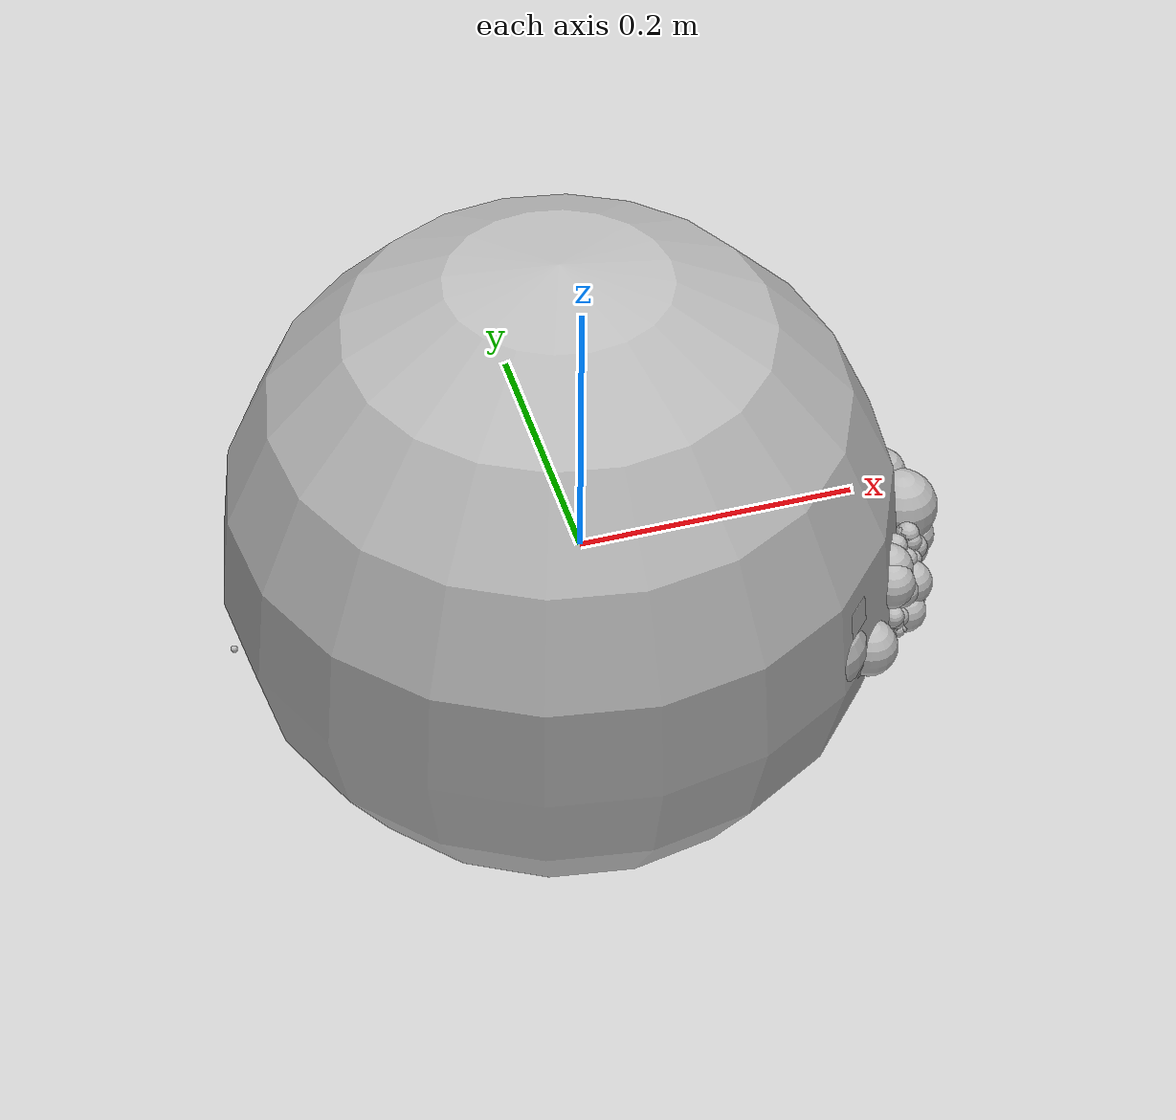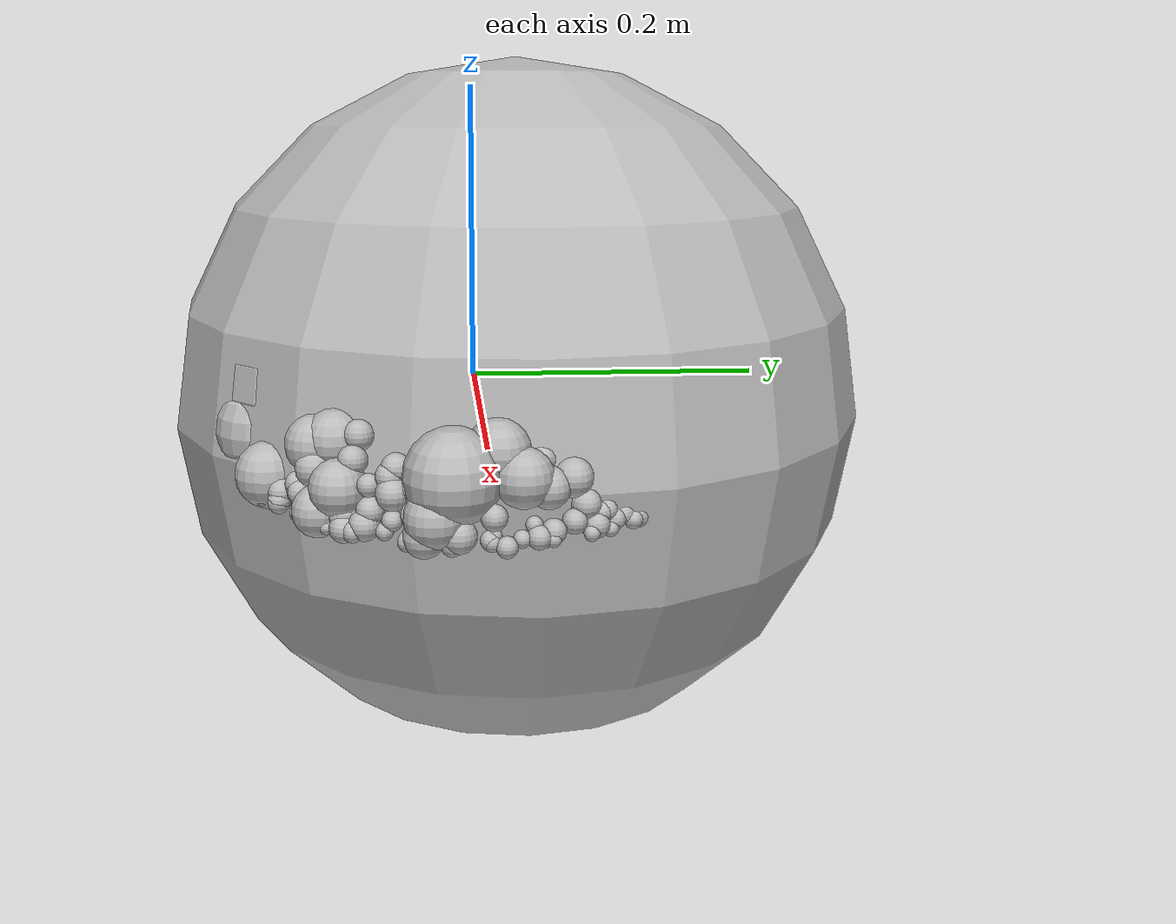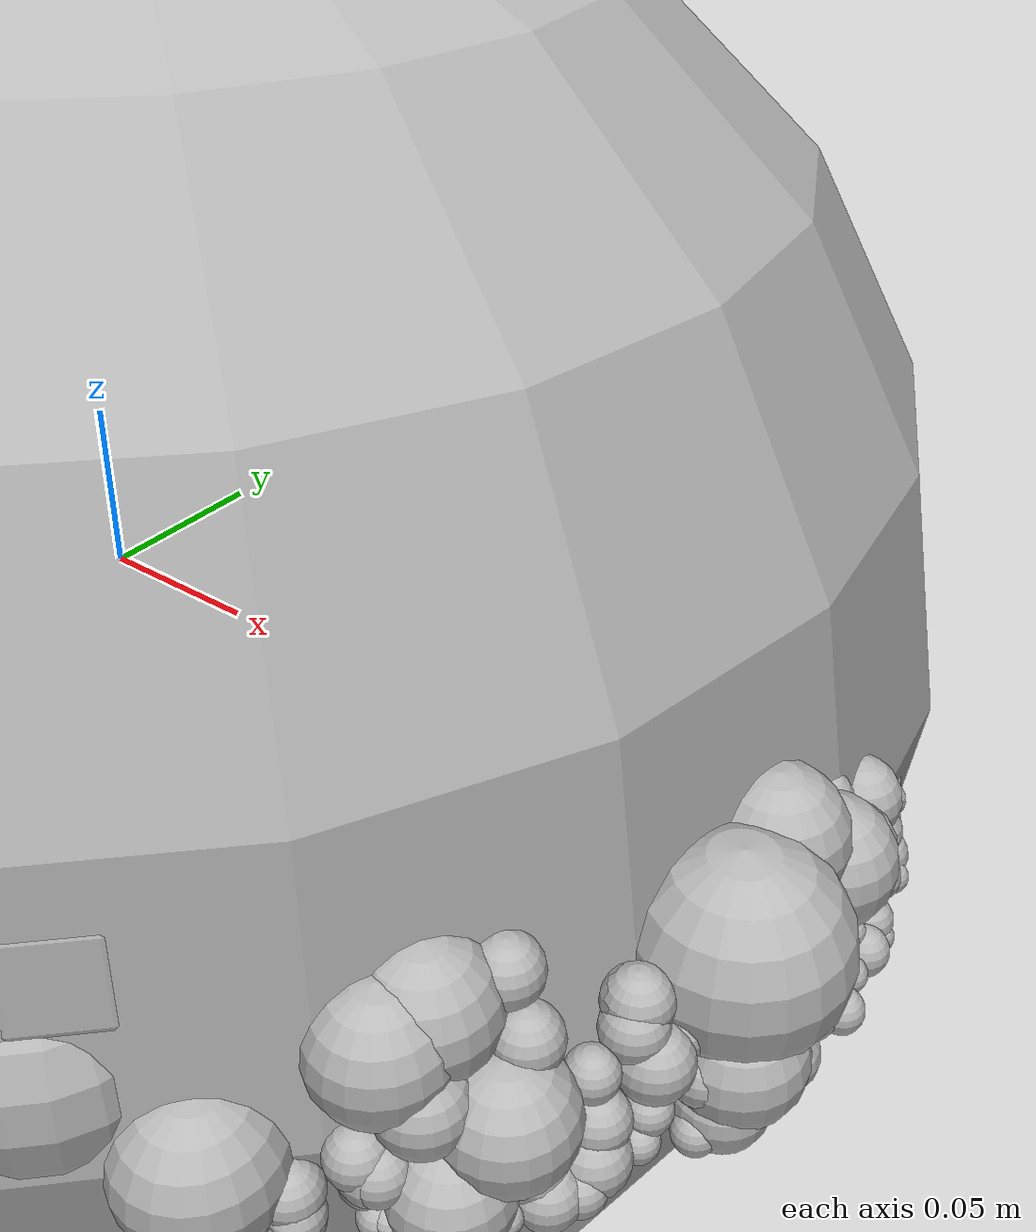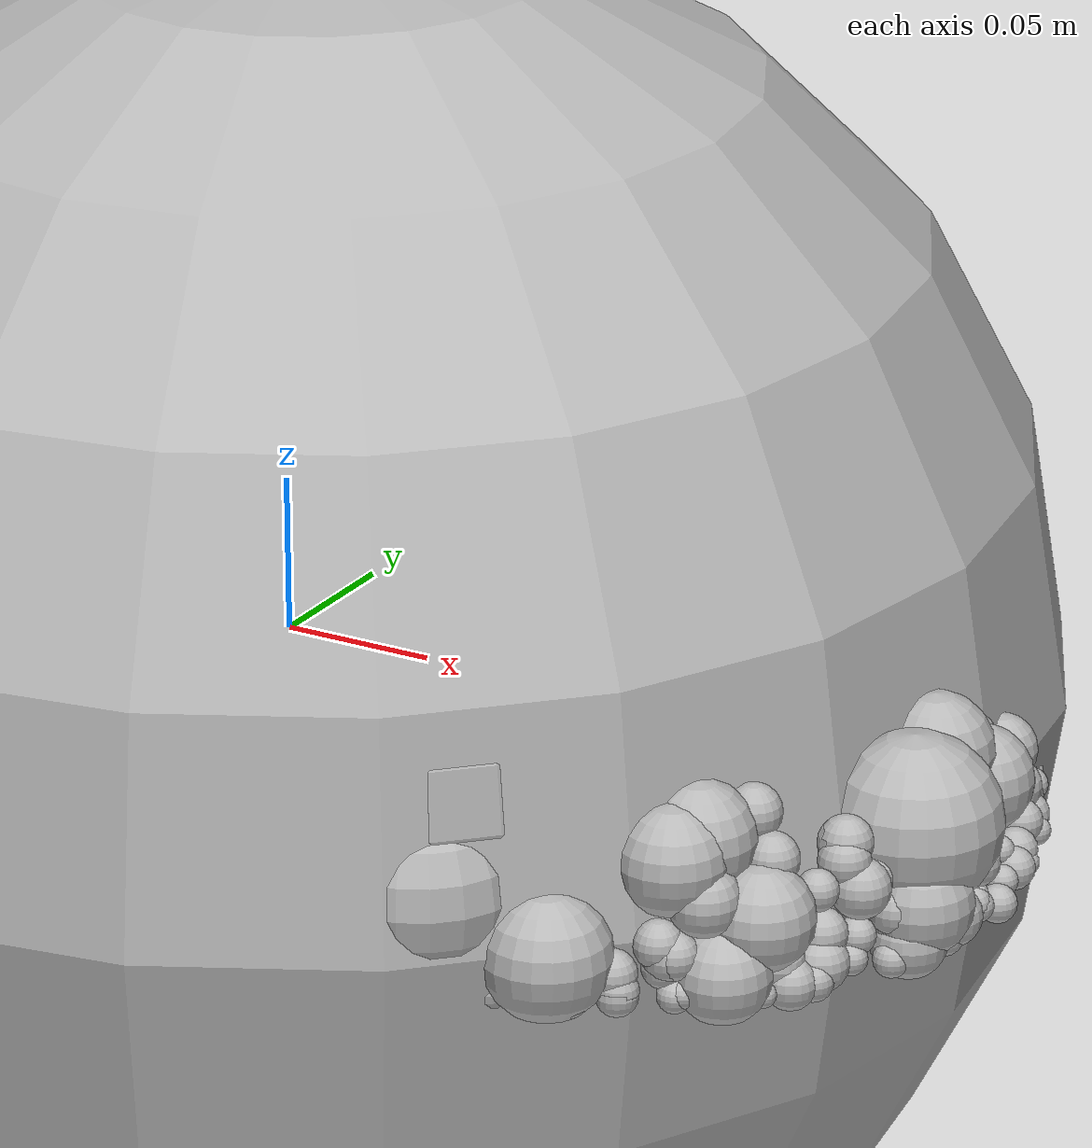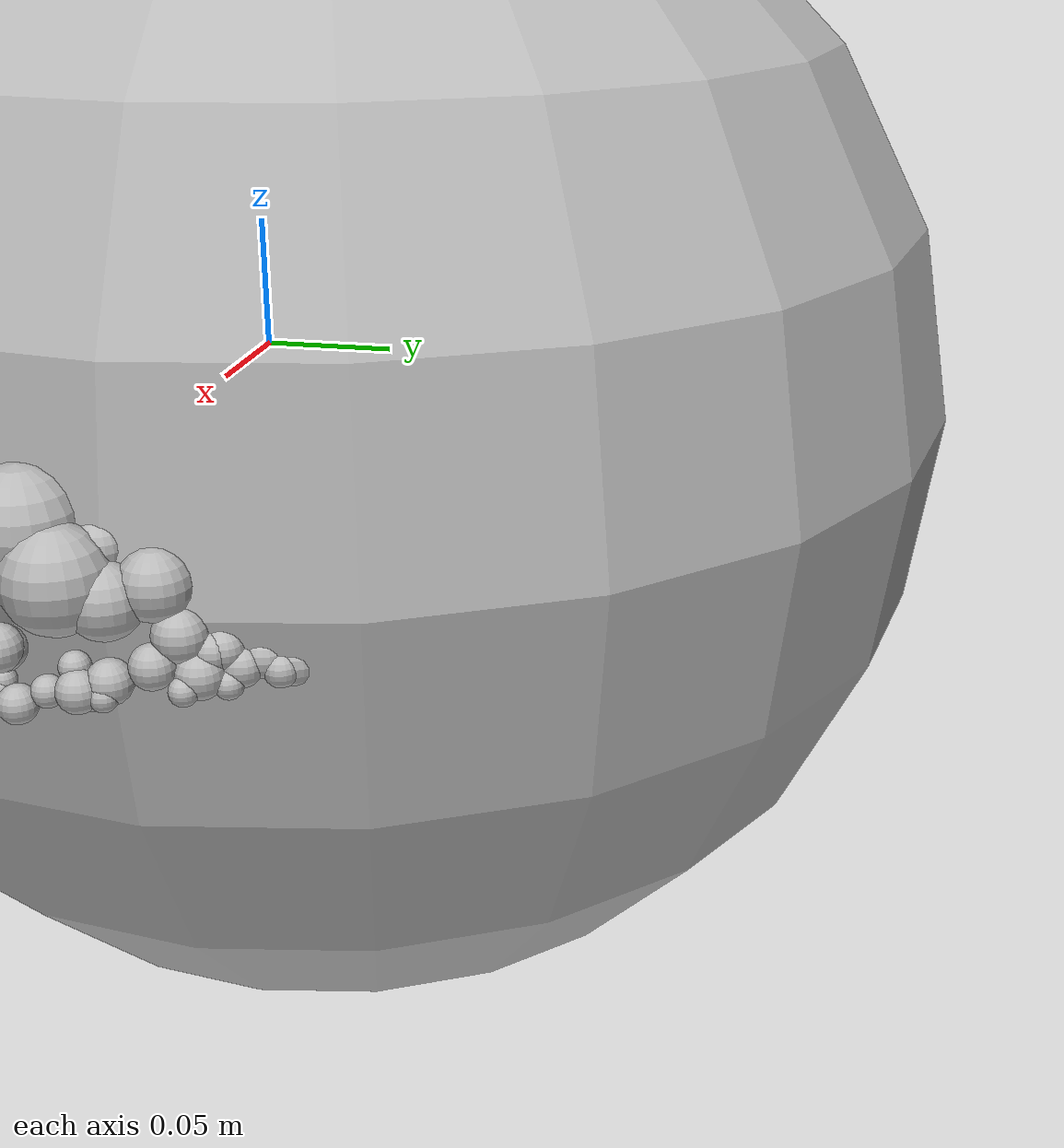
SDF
<?xml version='1.0'?>
<sdf version='1.6'>
	<model name='test.sph'>
	<static>false</static>
	<pose>0 0 0 0 0 0</pose>
		<link name='link'>
			<collision name='collision_0'>
				<pose>-0.00660952 0.0303351 -0.0193014 0 0 0</pose>
				<geometry>
					<sphere>
						<radius>0.238452</radius>
					</sphere>
				</geometry>
			</collision>
			<visual name='visual_0'>
				<pose>-0.00660952 0.0303351 -0.0193014 0 0 0</pose>
				<geometry>
					<sphere>
						<radius>0.238452</radius>
					</sphere>
				</geometry>
			</visual>
			<collision name='collision_1'>
				<pose>-0.00165144 -0.0609579 0.0239891 0 0 0</pose>
				<geometry>
					<sphere>
						<radius>0.0252161</radius>
					</sphere>
				</geometry>
			</collision>
			<visual name='visual_1'>
				<pose>-0.00165144 -0.0609579 0.0239891 0 0 0</pose>
				<geometry>
					<sphere>
						<radius>0.0252161</radius>
					</sphere>
				</geometry>
			</visual>
			<collision name='collision_2'>
				<pose>0.0281475 0.107814 0.00538855 0 0 0</pose>
				<geometry>
					<sphere>
						<radius>0.0444023</radius>
					</sphere>
				</geometry>
			</collision>
			<visual name='visual_2'>
				<pose>0.0281475 0.107814 0.00538855 0 0 0</pose>
				<geometry>
					<sphere>
						<radius>0.0444023</radius>
					</sphere>
				</geometry>
			</visual>
			<collision name='collision_3'>
				<pose>0.0131059 0.0933596 0.0146956 0 0 0</pose>
				<geometry>
					<sphere>
						<radius>0.00707587</radius>
					</sphere>
				</geometry>
			</collision>
			<visual name='visual_3'>
				<pose>0.0131059 0.0933596 0.0146956 0 0 0</pose>
				<geometry>
					<sphere>
						<radius>0.00707587</radius>
					</sphere>
				</geometry>
			</visual>
			<collision name='collision_4'>
				<pose>0.125572 -0.12894 -0.00477256 0 0 0</pose>
				<geometry>
					<sphere>
						<radius>0.0322774</radius>
					</sphere>
				</geometry>
			</collision>
			<visual name='visual_4'>
				<pose>0.125572 -0.12894 -0.00477256 0 0 0</pose>
				<geometry>
					<sphere>
						<radius>0.0322774</radius>
					</sphere>
				</geometry>
			</visual>
			<collision name='collision_5'>
				<pose>0.223776 0.00479134 0.00557033 0 0 0</pose>
				<geometry>
					<sphere>
						<radius>0.0184834</radius>
					</sphere>
				</geometry>
			</collision>
			<visual name='visual_5'>
				<pose>0.223776 0.00479134 0.00557033 0 0 0</pose>
				<geometry>
					<sphere>
						<radius>0.0184834</radius>
					</sphere>
				</geometry>
			</visual>
			<collision name='collision_6'>
				<pose>0.229395 -0.019602 -0.0062665 0 0 0</pose>
				<geometry>
					<sphere>
						<radius>0.0274804</radius>
					</sphere>
				</geometry>
			</collision>
			<visual name='visual_6'>
				<pose>0.229395 -0.019602 -0.0062665 0 0 0</pose>
				<geometry>
					<sphere>
						<radius>0.0274804</radius>
					</sphere>
				</geometry>
			</visual>
			<collision name='collision_7'>
				<pose>0.176943 0.108979 -0.00101988 0 0 0</pose>
				<geometry>
					<sphere>
						<radius>0.0225256</radius>
					</sphere>
				</geometry>
			</collision>
			<visual name='visual_7'>
				<pose>0.176943 0.108979 -0.00101988 0 0 0</pose>
				<geometry>
					<sphere>
						<radius>0.0225256</radius>
					</sphere>
				</geometry>
			</visual>
			<collision name='collision_8'>
				<pose>-0.00305181 0.0845897 0.0100366 0 0 0</pose>
				<geometry>
					<sphere>
						<radius>0.00811245</radius>
					</sphere>
				</geometry>
			</collision>
			<visual name='visual_8'>
				<pose>-0.00305181 0.0845897 0.0100366 0 0 0</pose>
				<geometry>
					<sphere>
						<radius>0.00811245</radius>
					</sphere>
				</geometry>
			</visual>
			<collision name='collision_9'>
				<pose>-0.00304109 0.0849429 0.00627902 0 0 0</pose>
				<geometry>
					<sphere>
						<radius>0.00740288</radius>
					</sphere>
				</geometry>
			</collision>
			<visual name='visual_9'>
				<pose>-0.00304109 0.0849429 0.00627902 0 0 0</pose>
				<geometry>
					<sphere>
						<radius>0.00740288</radius>
					</sphere>
				</geometry>
			</visual>
			<collision name='collision_10'>
				<pose>-0.0100048 0.0761118 0.013781 0 0 0</pose>
				<geometry>
					<sphere>
						<radius>0.00825998</radius>
					</sphere>
				</geometry>
			</collision>
			<visual name='visual_10'>
				<pose>-0.0100048 0.0761118 0.013781 0 0 0</pose>
				<geometry>
					<sphere>
						<radius>0.00825998</radius>
					</sphere>
				</geometry>
			</visual>
			<collision name='collision_11'>
				<pose>-0.00601012 0.0768157 0.0132385 0 0 0</pose>
				<geometry>
					<sphere>
						<radius>0.00672376</radius>
					</sphere>
				</geometry>
			</collision>
			<visual name='visual_11'>
				<pose>-0.00601012 0.0768157 0.0132385 0 0 0</pose>
				<geometry>
					<sphere>
						<radius>0.00672376</radius>
					</sphere>
				</geometry>
			</visual>
			<collision name='collision_12'>
				<pose>-0.0116245 0.0814209 0.00534139 0 0 0</pose>
				<geometry>
					<sphere>
						<radius>0.00814123</radius>
					</sphere>
				</geometry>
			</collision>
			<visual name='visual_12'>
				<pose>-0.0116245 0.0814209 0.00534139 0 0 0</pose>
				<geometry>
					<sphere>
						<radius>0.00814123</radius>
					</sphere>
				</geometry>
			</visual>
			<collision name='collision_13'>
				<pose>-0.00241446 0.0756885 0.0197477 0 0 0</pose>
				<geometry>
					<sphere>
						<radius>0.00700598</radius>
					</sphere>
				</geometry>
			</collision>
			<visual name='visual_13'>
				<pose>-0.00241446 0.0756885 0.0197477 0 0 0</pose>
				<geometry>
					<sphere>
						<radius>0.00700598</radius>
					</sphere>
				</geometry>
			</visual>
			<collision name='collision_14'>
				<pose>0.0210919 0.108282 0.0077997 0 0 0</pose>
				<geometry>
					<sphere>
						<radius>0.00806972</radius>
					</sphere>
				</geometry>
			</collision>
			<visual name='visual_14'>
				<pose>0.0210919 0.108282 0.0077997 0 0 0</pose>
				<geometry>
					<sphere>
						<radius>0.00806972</radius>
					</sphere>
				</geometry>
			</visual>
			<collision name='collision_15'>
				<pose>0.0194561 0.103428 0.0077366 0 0 0</pose>
				<geometry>
					<sphere>
						<radius>0.00693095</radius>
					</sphere>
				</geometry>
			</collision>
			<visual name='visual_15'>
				<pose>0.0194561 0.103428 0.0077366 0 0 0</pose>
				<geometry>
					<sphere>
						<radius>0.00693095</radius>
					</sphere>
				</geometry>
			</visual>
			<collision name='collision_16'>
				<pose>0.0908832 0.119789 0.0216014 0 0 0</pose>
				<geometry>
					<sphere>
						<radius>0.0108319</radius>
					</sphere>
				</geometry>
			</collision>
			<visual name='visual_16'>
				<pose>0.0908832 0.119789 0.0216014 0 0 0</pose>
				<geometry>
					<sphere>
						<radius>0.0108319</radius>
					</sphere>
				</geometry>
			</visual>
			<collision name='collision_17'>
				<pose>0.152701 0.128209 -0.0163977 0 0 0</pose>
				<geometry>
					<sphere>
						<radius>0.00910525</radius>
					</sphere>
				</geometry>
			</collision>
			<visual name='visual_17'>
				<pose>0.152701 0.128209 -0.0163977 0 0 0</pose>
				<geometry>
					<sphere>
						<radius>0.00910525</radius>
					</sphere>
				</geometry>
			</visual>
			<collision name='collision_18'>
				<pose>0.152865 0.12446 -0.00355444 0 0 0</pose>
				<geometry>
					<sphere>
						<radius>0.00818079</radius>
					</sphere>
				</geometry>
			</collision>
			<visual name='visual_18'>
				<pose>0.152865 0.12446 -0.00355444 0 0 0</pose>
				<geometry>
					<sphere>
						<radius>0.00818079</radius>
					</sphere>
				</geometry>
			</visual>
			<collision name='collision_19'>
				<pose>0.145744 0.114488 0.0154926 0 0 0</pose>
				<geometry>
					<sphere>
						<radius>0.00621431</radius>
					</sphere>
				</geometry>
			</collision>
			<visual name='visual_19'>
				<pose>0.145744 0.114488 0.0154926 0 0 0</pose>
				<geometry>
					<sphere>
						<radius>0.00621431</radius>
					</sphere>
				</geometry>
			</visual>
			<collision name='collision_20'>
				<pose>0.153274 0.119918 0.000249846 0 0 0</pose>
				<geometry>
					<sphere>
						<radius>0.00735193</radius>
					</sphere>
				</geometry>
			</collision>
			<visual name='visual_20'>
				<pose>0.153274 0.119918 0.000249846 0 0 0</pose>
				<geometry>
					<sphere>
						<radius>0.00735193</radius>
					</sphere>
				</geometry>
			</visual>
			<collision name='collision_21'>
				<pose>0.156977 0.112544 0.00978986 0 0 0</pose>
				<geometry>
					<sphere>
						<radius>0.00695936</radius>
					</sphere>
				</geometry>
			</collision>
			<visual name='visual_21'>
				<pose>0.156977 0.112544 0.00978986 0 0 0</pose>
				<geometry>
					<sphere>
						<radius>0.00695936</radius>
					</sphere>
				</geometry>
			</visual>
			<collision name='collision_22'>
				<pose>0.163795 0.121345 -0.00980629 0 0 0</pose>
				<geometry>
					<sphere>
						<radius>0.00905869</radius>
					</sphere>
				</geometry>
			</collision>
			<visual name='visual_22'>
				<pose>0.163795 0.121345 -0.00980629 0 0 0</pose>
				<geometry>
					<sphere>
						<radius>0.00905869</radius>
					</sphere>
				</geometry>
			</visual>
			<collision name='collision_23'>
				<pose>0.162473 0.126357 -0.0227513 0 0 0</pose>
				<geometry>
					<sphere>
						<radius>0.00612547</radius>
					</sphere>
				</geometry>
			</collision>
			<visual name='visual_23'>
				<pose>0.162473 0.126357 -0.0227513 0 0 0</pose>
				<geometry>
					<sphere>
						<radius>0.00612547</radius>
					</sphere>
				</geometry>
			</visual>
			<collision name='collision_24'>
				<pose>-0.0358302 0.042242 -0.00815999 0 0 0</pose>
				<geometry>
					<sphere>
						<radius>0.00516498</radius>
					</sphere>
				</geometry>
			</collision>
			<visual name='visual_24'>
				<pose>-0.0358302 0.042242 -0.00815999 0 0 0</pose>
				<geometry>
					<sphere>
						<radius>0.00516498</radius>
					</sphere>
				</geometry>
			</visual>
			<collision name='collision_25'>
				<pose>-0.0360902 0.0202083 -0.00367824 0 0 0</pose>
				<geometry>
					<sphere>
						<radius>0.00770931</radius>
					</sphere>
				</geometry>
			</collision>
			<visual name='visual_25'>
				<pose>-0.0360902 0.0202083 -0.00367824 0 0 0</pose>
				<geometry>
					<sphere>
						<radius>0.00770931</radius>
					</sphere>
				</geometry>
			</visual>
			<collision name='collision_26'>
				<pose>-0.0366259 0.0197578 -0.00309751 0 0 0</pose>
				<geometry>
					<sphere>
						<radius>0.00778593</radius>
					</sphere>
				</geometry>
			</collision>
			<visual name='visual_26'>
				<pose>-0.0366259 0.0197578 -0.00309751 0 0 0</pose>
				<geometry>
					<sphere>
						<radius>0.00778593</radius>
					</sphere>
				</geometry>
			</visual>
			<collision name='collision_27'>
				<pose>-0.0245753 -0.0363193 0.0190252 0 0 0</pose>
				<geometry>
					<sphere>
						<radius>0.00682132</radius>
					</sphere>
				</geometry>
			</collision>
			<visual name='visual_27'>
				<pose>-0.0245753 -0.0363193 0.0190252 0 0 0</pose>
				<geometry>
					<sphere>
						<radius>0.00682132</radius>
					</sphere>
				</geometry>
			</visual>
			<collision name='collision_28'>
				<pose>-0.024398 -0.0356761 0.017417 0 0 0</pose>
				<geometry>
					<sphere>
						<radius>0.0063594</radius>
					</sphere>
				</geometry>
			</collision>
			<visual name='visual_28'>
				<pose>-0.024398 -0.0356761 0.017417 0 0 0</pose>
				<geometry>
					<sphere>
						<radius>0.0063594</radius>
					</sphere>
				</geometry>
			</visual>
			<collision name='collision_29'>
				<pose>-0.0234874 -0.0350958 0.0169614 0 0 0</pose>
				<geometry>
					<sphere>
						<radius>0.00640671</radius>
					</sphere>
				</geometry>
			</collision>
			<visual name='visual_29'>
				<pose>-0.0234874 -0.0350958 0.0169614 0 0 0</pose>
				<geometry>
					<sphere>
						<radius>0.00640671</radius>
					</sphere>
				</geometry>
			</visual>
			<collision name='collision_30'>
				<pose>0.0697679 -0.00822361 0.0311398 0 0 0</pose>
				<geometry>
					<sphere>
						<radius>0.01626</radius>
					</sphere>
				</geometry>
			</collision>
			<visual name='visual_30'>
				<pose>0.0697679 -0.00822361 0.0311398 0 0 0</pose>
				<geometry>
					<sphere>
						<radius>0.01626</radius>
					</sphere>
				</geometry>
			</visual>
			<collision name='collision_31'>
				<pose>0.0907154 -0.021962 0.0291856 0 0 0</pose>
				<geometry>
					<sphere>
						<radius>0.0143569</radius>
					</sphere>
				</geometry>
			</collision>
			<visual name='visual_31'>
				<pose>0.0907154 -0.021962 0.0291856 0 0 0</pose>
				<geometry>
					<sphere>
						<radius>0.0143569</radius>
					</sphere>
				</geometry>
			</visual>
			<collision name='collision_32'>
				<pose>0.106869 -0.00953804 0.0288572 0 0 0</pose>
				<geometry>
					<sphere>
						<radius>0.0164324</radius>
					</sphere>
				</geometry>
			</collision>
			<visual name='visual_32'>
				<pose>0.106869 -0.00953804 0.0288572 0 0 0</pose>
				<geometry>
					<sphere>
						<radius>0.0164324</radius>
					</sphere>
				</geometry>
			</visual>
			<collision name='collision_33'>
				<pose>0.106747 -0.0147494 0.0271713 0 0 0</pose>
				<geometry>
					<sphere>
						<radius>0.0120241</radius>
					</sphere>
				</geometry>
			</collision>
			<visual name='visual_33'>
				<pose>0.106747 -0.0147494 0.0271713 0 0 0</pose>
				<geometry>
					<sphere>
						<radius>0.0120241</radius>
					</sphere>
				</geometry>
			</visual>
			<collision name='collision_34'>
				<pose>0.089057 -0.0101986 0.0298843 0 0 0</pose>
				<geometry>
					<sphere>
						<radius>0.0150122</radius>
					</sphere>
				</geometry>
			</collision>
			<visual name='visual_34'>
				<pose>0.089057 -0.0101986 0.0298843 0 0 0</pose>
				<geometry>
					<sphere>
						<radius>0.0150122</radius>
					</sphere>
				</geometry>
			</visual>
			<collision name='collision_35'>
				<pose>0.090253 -0.0390018 0.0303045 0 0 0</pose>
				<geometry>
					<sphere>
						<radius>0.0142019</radius>
					</sphere>
				</geometry>
			</collision>
			<visual name='visual_35'>
				<pose>0.090253 -0.0390018 0.0303045 0 0 0</pose>
				<geometry>
					<sphere>
						<radius>0.0142019</radius>
					</sphere>
				</geometry>
			</visual>
			<collision name='collision_36'>
				<pose>0.153913 -0.026932 0.0232232 0 0 0</pose>
				<geometry>
					<sphere>
						<radius>0.0116333</radius>
					</sphere>
				</geometry>
			</collision>
			<visual name='visual_36'>
				<pose>0.153913 -0.026932 0.0232232 0 0 0</pose>
				<geometry>
					<sphere>
						<radius>0.0116333</radius>
					</sphere>
				</geometry>
			</visual>
			<collision name='collision_37'>
				<pose>0.146319 -0.0441628 0.0201949 0 0 0</pose>
				<geometry>
					<sphere>
						<radius>0.012348</radius>
					</sphere>
				</geometry>
			</collision>
			<visual name='visual_37'>
				<pose>0.146319 -0.0441628 0.0201949 0 0 0</pose>
				<geometry>
					<sphere>
						<radius>0.012348</radius>
					</sphere>
				</geometry>
			</visual>
			<collision name='collision_38'>
				<pose>0.0369695 -0.101909 0.023099 0 0 0</pose>
				<geometry>
					<sphere>
						<radius>0.0130398</radius>
					</sphere>
				</geometry>
			</collision>
			<visual name='visual_38'>
				<pose>0.0369695 -0.101909 0.023099 0 0 0</pose>
				<geometry>
					<sphere>
						<radius>0.0130398</radius>
					</sphere>
				</geometry>
			</visual>
			<collision name='collision_39'>
				<pose>0.0512319 -0.116396 0.0143298 0 0 0</pose>
				<geometry>
					<sphere>
						<radius>0.0220772</radius>
					</sphere>
				</geometry>
			</collision>
			<visual name='visual_39'>
				<pose>0.0512319 -0.116396 0.0143298 0 0 0</pose>
				<geometry>
					<sphere>
						<radius>0.0220772</radius>
					</sphere>
				</geometry>
			</visual>
			<collision name='collision_40'>
				<pose>0.101784 -0.0943799 0.0168263 0 0 0</pose>
				<geometry>
					<sphere>
						<radius>0.0661</radius>
					</sphere>
				</geometry>
			</collision>
			<visual name='visual_40'>
				<pose>0.101784 -0.0943799 0.0168263 0 0 0</pose>
				<geometry>
					<sphere>
						<radius>0.0661</radius>
					</sphere>
				</geometry>
			</visual>
			<collision name='collision_41'>
				<pose>0.0971478 -0.0679178 0.0287506 0 0 0</pose>
				<geometry>
					<sphere>
						<radius>0.0278731</radius>
					</sphere>
				</geometry>
			</collision>
			<visual name='visual_41'>
				<pose>0.0971478 -0.0679178 0.0287506 0 0 0</pose>
				<geometry>
					<sphere>
						<radius>0.0278731</radius>
					</sphere>
				</geometry>
			</visual>
			<collision name='collision_42'>
				<pose>0.0907383 -0.128811 0.00848675 0 0 0</pose>
				<geometry>
					<sphere>
						<radius>0.0154286</radius>
					</sphere>
				</geometry>
			</collision>
			<visual name='visual_42'>
				<pose>0.0907383 -0.128811 0.00848675 0 0 0</pose>
				<geometry>
					<sphere>
						<radius>0.0154286</radius>
					</sphere>
				</geometry>
			</visual>
			<collision name='collision_43'>
				<pose>0.11985 -0.140335 -0.0139216 0 0 0</pose>
				<geometry>
					<sphere>
						<radius>0.0200256</radius>
					</sphere>
				</geometry>
			</collision>
			<visual name='visual_43'>
				<pose>0.11985 -0.140335 -0.0139216 0 0 0</pose>
				<geometry>
					<sphere>
						<radius>0.0200256</radius>
					</sphere>
				</geometry>
			</visual>
			<collision name='collision_44'>
				<pose>0.0996684 -0.139316 -0.0121816 0 0 0</pose>
				<geometry>
					<sphere>
						<radius>0.0197189</radius>
					</sphere>
				</geometry>
			</collision>
			<visual name='visual_44'>
				<pose>0.0996684 -0.139316 -0.0121816 0 0 0</pose>
				<geometry>
					<sphere>
						<radius>0.0197189</radius>
					</sphere>
				</geometry>
			</visual>
			<collision name='collision_45'>
				<pose>0.164963 -0.124865 -0.0219835 0 0 0</pose>
				<geometry>
					<sphere>
						<radius>0.0200432</radius>
					</sphere>
				</geometry>
			</collision>
			<visual name='visual_45'>
				<pose>0.164963 -0.124865 -0.0219835 0 0 0</pose>
				<geometry>
					<sphere>
						<radius>0.0200432</radius>
					</sphere>
				</geometry>
			</visual>
			<collision name='collision_46'>
				<pose>0.226429 0.0451464 -0.00881775 0 0 0</pose>
				<geometry>
					<sphere>
						<radius>0.0112676</radius>
					</sphere>
				</geometry>
			</collision>
			<visual name='visual_46'>
				<pose>0.226429 0.0451464 -0.00881775 0 0 0</pose>
				<geometry>
					<sphere>
						<radius>0.0112676</radius>
					</sphere>
				</geometry>
			</visual>
			<collision name='collision_47'>
				<pose>0.231443 0.0317266 -0.0128309 0 0 0</pose>
				<geometry>
					<sphere>
						<radius>0.0119223</radius>
					</sphere>
				</geometry>
			</collision>
			<visual name='visual_47'>
				<pose>0.231443 0.0317266 -0.0128309 0 0 0</pose>
				<geometry>
					<sphere>
						<radius>0.0119223</radius>
					</sphere>
				</geometry>
			</visual>
			<collision name='collision_48'>
				<pose>0.232322 0.0180073 -0.00676918 0 0 0</pose>
				<geometry>
					<sphere>
						<radius>0.0169032</radius>
					</sphere>
				</geometry>
			</collision>
			<visual name='visual_48'>
				<pose>0.232322 0.0180073 -0.00676918 0 0 0</pose>
				<geometry>
					<sphere>
						<radius>0.0169032</radius>
					</sphere>
				</geometry>
			</visual>
			<collision name='collision_49'>
				<pose>0.241108 -0.0167799 -0.0357592 0 0 0</pose>
				<geometry>
					<sphere>
						<radius>0.00965415</radius>
					</sphere>
				</geometry>
			</collision>
			<visual name='visual_49'>
				<pose>0.241108 -0.0167799 -0.0357592 0 0 0</pose>
				<geometry>
					<sphere>
						<radius>0.00965415</radius>
					</sphere>
				</geometry>
			</visual>
			<collision name='collision_50'>
				<pose>0.236642 -0.0353179 -0.0369949 0 0 0</pose>
				<geometry>
					<sphere>
						<radius>0.0119711</radius>
					</sphere>
				</geometry>
			</collision>
			<visual name='visual_50'>
				<pose>0.236642 -0.0353179 -0.0369949 0 0 0</pose>
				<geometry>
					<sphere>
						<radius>0.0119711</radius>
					</sphere>
				</geometry>
			</visual>
			<collision name='collision_51'>
				<pose>0.240751 -0.020578 -0.0408465 0 0 0</pose>
				<geometry>
					<sphere>
						<radius>0.00631152</radius>
					</sphere>
				</geometry>
			</collision>
			<visual name='visual_51'>
				<pose>0.240751 -0.020578 -0.0408465 0 0 0</pose>
				<geometry>
					<sphere>
						<radius>0.00631152</radius>
					</sphere>
				</geometry>
			</visual>
			<collision name='collision_52'>
				<pose>0.236883 -0.0299228 -0.0268655 0 0 0</pose>
				<geometry>
					<sphere>
						<radius>0.0169253</radius>
					</sphere>
				</geometry>
			</collision>
			<visual name='visual_52'>
				<pose>0.236883 -0.0299228 -0.0268655 0 0 0</pose>
				<geometry>
					<sphere>
						<radius>0.0169253</radius>
					</sphere>
				</geometry>
			</visual>
			<collision name='collision_53'>
				<pose>0.23427 -0.0397985 -0.0258062 0 0 0</pose>
				<geometry>
					<sphere>
						<radius>0.0082545</radius>
					</sphere>
				</geometry>
			</collision>
			<visual name='visual_53'>
				<pose>0.23427 -0.0397985 -0.0258062 0 0 0</pose>
				<geometry>
					<sphere>
						<radius>0.0082545</radius>
					</sphere>
				</geometry>
			</visual>
			<collision name='collision_54'>
				<pose>0.189854 -0.0956509 0.00232234 0 0 0</pose>
				<geometry>
					<sphere>
						<radius>0.0171191</radius>
					</sphere>
				</geometry>
			</collision>
			<visual name='visual_54'>
				<pose>0.189854 -0.0956509 0.00232234 0 0 0</pose>
				<geometry>
					<sphere>
						<radius>0.0171191</radius>
					</sphere>
				</geometry>
			</visual>
			<collision name='collision_55'>
				<pose>0.200282 -0.0951618 -0.00842022 0 0 0</pose>
				<geometry>
					<sphere>
						<radius>0.0112298</radius>
					</sphere>
				</geometry>
			</collision>
			<visual name='visual_55'>
				<pose>0.200282 -0.0951618 -0.00842022 0 0 0</pose>
				<geometry>
					<sphere>
						<radius>0.0112298</radius>
					</sphere>
				</geometry>
			</visual>
			<collision name='collision_56'>
				<pose>0.192189 -0.0842883 0.00551374 0 0 0</pose>
				<geometry>
					<sphere>
						<radius>0.0176894</radius>
					</sphere>
				</geometry>
			</collision>
			<visual name='visual_56'>
				<pose>0.192189 -0.0842883 0.00551374 0 0 0</pose>
				<geometry>
					<sphere>
						<radius>0.0176894</radius>
					</sphere>
				</geometry>
			</visual>
			<collision name='collision_57'>
				<pose>0.210826 -0.073719 -0.00158535 0 0 0</pose>
				<geometry>
					<sphere>
						<radius>0.00851978</radius>
					</sphere>
				</geometry>
			</collision>
			<visual name='visual_57'>
				<pose>0.210826 -0.073719 -0.00158535 0 0 0</pose>
				<geometry>
					<sphere>
						<radius>0.00851978</radius>
					</sphere>
				</geometry>
			</visual>
			<collision name='collision_58'>
				<pose>0.202861 -0.070422 0.0104564 0 0 0</pose>
				<geometry>
					<sphere>
						<radius>0.00879239</radius>
					</sphere>
				</geometry>
			</collision>
			<visual name='visual_58'>
				<pose>0.202861 -0.070422 0.0104564 0 0 0</pose>
				<geometry>
					<sphere>
						<radius>0.00879239</radius>
					</sphere>
				</geometry>
			</visual>
			<collision name='collision_59'>
				<pose>0.211817 -0.0818102 -0.0165698 0 0 0</pose>
				<geometry>
					<sphere>
						<radius>0.0164844</radius>
					</sphere>
				</geometry>
			</collision>
			<visual name='visual_59'>
				<pose>0.211817 -0.0818102 -0.0165698 0 0 0</pose>
				<geometry>
					<sphere>
						<radius>0.0164844</radius>
					</sphere>
				</geometry>
			</visual>
			<collision name='collision_60'>
				<pose>0.221447 -0.0649617 -0.0125699 0 0 0</pose>
				<geometry>
					<sphere>
						<radius>0.00648395</radius>
					</sphere>
				</geometry>
			</collision>
			<visual name='visual_60'>
				<pose>0.221447 -0.0649617 -0.0125699 0 0 0</pose>
				<geometry>
					<sphere>
						<radius>0.00648395</radius>
					</sphere>
				</geometry>
			</visual>
			<collision name='collision_61'>
				<pose>0.205821 -0.0936657 -0.0314673 0 0 0</pose>
				<geometry>
					<sphere>
						<radius>0.0149594</radius>
					</sphere>
				</geometry>
			</collision>
			<visual name='visual_61'>
				<pose>0.205821 -0.0936657 -0.0314673 0 0 0</pose>
				<geometry>
					<sphere>
						<radius>0.0149594</radius>
					</sphere>
				</geometry>
			</visual>
			<collision name='collision_62'>
				<pose>0.0804474 -0.134681 -0.0014736 0 0 0</pose>
				<geometry>
					<sphere>
						<radius>0.00870504</radius>
					</sphere>
				</geometry>
			</collision>
			<visual name='visual_62'>
				<pose>0.0804474 -0.134681 -0.0014736 0 0 0</pose>
				<geometry>
					<sphere>
						<radius>0.00870504</radius>
					</sphere>
				</geometry>
			</visual>
			<collision name='collision_63'>
				<pose>0.0924387 -0.137083 0.000732128 0 0 0</pose>
				<geometry>
					<sphere>
						<radius>0.0078247</radius>
					</sphere>
				</geometry>
			</collision>
			<visual name='visual_63'>
				<pose>0.0924387 -0.137083 0.000732128 0 0 0</pose>
				<geometry>
					<sphere>
						<radius>0.0078247</radius>
					</sphere>
				</geometry>
			</visual>
			<collision name='collision_64'>
				<pose>0.0889998 -0.139443 -0.0200478 0 0 0</pose>
				<geometry>
					<sphere>
						<radius>0.00480158</radius>
					</sphere>
				</geometry>
			</collision>
			<visual name='visual_64'>
				<pose>0.0889998 -0.139443 -0.0200478 0 0 0</pose>
				<geometry>
					<sphere>
						<radius>0.00480158</radius>
					</sphere>
				</geometry>
			</visual>
			<collision name='collision_65'>
				<pose>0.0837583 -0.142118 -0.0224406 0 0 0</pose>
				<geometry>
					<sphere>
						<radius>0.00684947</radius>
					</sphere>
				</geometry>
			</collision>
			<visual name='visual_65'>
				<pose>0.0837583 -0.142118 -0.0224406 0 0 0</pose>
				<geometry>
					<sphere>
						<radius>0.00684947</radius>
					</sphere>
				</geometry>
			</visual>
			<collision name='collision_66'>
				<pose>0.0842961 -0.138965 -0.00944856 0 0 0</pose>
				<geometry>
					<sphere>
						<radius>0.00737238</radius>
					</sphere>
				</geometry>
			</collision>
			<visual name='visual_66'>
				<pose>0.0842961 -0.138965 -0.00944856 0 0 0</pose>
				<geometry>
					<sphere>
						<radius>0.00737238</radius>
					</sphere>
				</geometry>
			</visual>
			<collision name='collision_67'>
				<pose>0.0736704 -0.139294 -0.0145146 0 0 0</pose>
				<geometry>
					<sphere>
						<radius>0.00655819</radius>
					</sphere>
				</geometry>
			</collision>
			<visual name='visual_67'>
				<pose>0.0736704 -0.139294 -0.0145146 0 0 0</pose>
				<geometry>
					<sphere>
						<radius>0.00655819</radius>
					</sphere>
				</geometry>
			</visual>
			<collision name='collision_68'>
				<pose>0.0723396 -0.135103 -0.00916057 0 0 0</pose>
				<geometry>
					<sphere>
						<radius>0.00735869</radius>
					</sphere>
				</geometry>
			</collision>
			<visual name='visual_68'>
				<pose>0.0723396 -0.135103 -0.00916057 0 0 0</pose>
				<geometry>
					<sphere>
						<radius>0.00735869</radius>
					</sphere>
				</geometry>
			</visual>
			<collision name='collision_69'>
				<pose>0.073419 -0.143908 -0.0223485 0 0 0</pose>
				<geometry>
					<sphere>
						<radius>0.00436263</radius>
					</sphere>
				</geometry>
			</collision>
			<visual name='visual_69'>
				<pose>0.073419 -0.143908 -0.0223485 0 0 0</pose>
				<geometry>
					<sphere>
						<radius>0.00436263</radius>
					</sphere>
				</geometry>
			</visual>
			<collision name='collision_70'>
				<pose>0.0518197 -0.135345 -0.0204397 0 0 0</pose>
				<geometry>
					<sphere>
						<radius>0.0072655</radius>
					</sphere>
				</geometry>
			</collision>
			<visual name='visual_70'>
				<pose>0.0518197 -0.135345 -0.0204397 0 0 0</pose>
				<geometry>
					<sphere>
						<radius>0.0072655</radius>
					</sphere>
				</geometry>
			</visual>
			<collision name='collision_71'>
				<pose>0.0599447 -0.135052 -0.0177827 0 0 0</pose>
				<geometry>
					<sphere>
						<radius>0.00803942</radius>
					</sphere>
				</geometry>
			</collision>
			<visual name='visual_71'>
				<pose>0.0599447 -0.135052 -0.0177827 0 0 0</pose>
				<geometry>
					<sphere>
						<radius>0.00803942</radius>
					</sphere>
				</geometry>
			</visual>
			<collision name='collision_72'>
				<pose>0.0634617 -0.134533 -0.0172439 0 0 0</pose>
				<geometry>
					<sphere>
						<radius>0.00712815</radius>
					</sphere>
				</geometry>
			</collision>
			<visual name='visual_72'>
				<pose>0.0634617 -0.134533 -0.0172439 0 0 0</pose>
				<geometry>
					<sphere>
						<radius>0.00712815</radius>
					</sphere>
				</geometry>
			</visual>
			<collision name='collision_73'>
				<pose>0.0660618 -0.138859 -0.0239809 0 0 0</pose>
				<geometry>
					<sphere>
						<radius>0.00843724</radius>
					</sphere>
				</geometry>
			</collision>
			<visual name='visual_73'>
				<pose>0.0660618 -0.138859 -0.0239809 0 0 0</pose>
				<geometry>
					<sphere>
						<radius>0.00843724</radius>
					</sphere>
				</geometry>
			</visual>
			<collision name='collision_74'>
				<pose>0.0395178 -0.131729 -0.0197207 0 0 0</pose>
				<geometry>
					<sphere>
						<radius>0.0109245</radius>
					</sphere>
				</geometry>
			</collision>
			<visual name='visual_74'>
				<pose>0.0395178 -0.131729 -0.0197207 0 0 0</pose>
				<geometry>
					<sphere>
						<radius>0.0109245</radius>
					</sphere>
				</geometry>
			</visual>
			<collision name='collision_75'>
				<pose>0.0351654 -0.122405 -0.0103964 0 0 0</pose>
				<geometry>
					<sphere>
						<radius>0.0092784</radius>
					</sphere>
				</geometry>
			</collision>
			<visual name='visual_75'>
				<pose>0.0351654 -0.122405 -0.0103964 0 0 0</pose>
				<geometry>
					<sphere>
						<radius>0.0092784</radius>
					</sphere>
				</geometry>
			</visual>
			<collision name='collision_76'>
				<pose>0.0492518 -0.129385 -0.00526611 0 0 0</pose>
				<geometry>
					<sphere>
						<radius>0.0126754</radius>
					</sphere>
				</geometry>
			</collision>
			<visual name='visual_76'>
				<pose>0.0492518 -0.129385 -0.00526611 0 0 0</pose>
				<geometry>
					<sphere>
						<radius>0.0126754</radius>
					</sphere>
				</geometry>
			</visual>
			<collision name='collision_77'>
				<pose>0.044311 -0.12723 -0.0148974 0 0 0</pose>
				<geometry>
					<sphere>
						<radius>0.00639596</radius>
					</sphere>
				</geometry>
			</collision>
			<visual name='visual_77'>
				<pose>0.044311 -0.12723 -0.0148974 0 0 0</pose>
				<geometry>
					<sphere>
						<radius>0.00639596</radius>
					</sphere>
				</geometry>
			</visual>
			<collision name='collision_78'>
				<pose>0.0531467 -0.104724 0.0227779 0 0 0</pose>
				<geometry>
					<sphere>
						<radius>0.00780575</radius>
					</sphere>
				</geometry>
			</collision>
			<visual name='visual_78'>
				<pose>0.0531467 -0.104724 0.0227779 0 0 0</pose>
				<geometry>
					<sphere>
						<radius>0.00780575</radius>
					</sphere>
				</geometry>
			</visual>
			<collision name='collision_79'>
				<pose>0.0531427 -0.10548 0.0232452 0 0 0</pose>
				<geometry>
					<sphere>
						<radius>0.00763094</radius>
					</sphere>
				</geometry>
			</collision>
			<visual name='visual_79'>
				<pose>0.0531427 -0.10548 0.0232452 0 0 0</pose>
				<geometry>
					<sphere>
						<radius>0.00763094</radius>
					</sphere>
				</geometry>
			</visual>
			<collision name='collision_80'>
				<pose>0.0522139 -0.106061 0.0237937 0 0 0</pose>
				<geometry>
					<sphere>
						<radius>0.00731803</radius>
					</sphere>
				</geometry>
			</collision>
			<visual name='visual_80'>
				<pose>0.0522139 -0.106061 0.0237937 0 0 0</pose>
				<geometry>
					<sphere>
						<radius>0.00731803</radius>
					</sphere>
				</geometry>
			</visual>
			<collision name='collision_81'>
				<pose>0.0669406 -0.110861 0.0250331 0 0 0</pose>
				<geometry>
					<sphere>
						<radius>0.0082094</radius>
					</sphere>
				</geometry>
			</collision>
			<visual name='visual_81'>
				<pose>0.0669406 -0.110861 0.0250331 0 0 0</pose>
				<geometry>
					<sphere>
						<radius>0.0082094</radius>
					</sphere>
				</geometry>
			</visual>
			<collision name='collision_82'>
				<pose>0.0679077 -0.10637 0.0233636 0 0 0</pose>
				<geometry>
					<sphere>
						<radius>0.0081031</radius>
					</sphere>
				</geometry>
			</collision>
			<visual name='visual_82'>
				<pose>0.0679077 -0.10637 0.0233636 0 0 0</pose>
				<geometry>
					<sphere>
						<radius>0.0081031</radius>
					</sphere>
				</geometry>
			</visual>
			<collision name='collision_83'>
				<pose>0.133392 -0.110928 0.0181267 0 0 0</pose>
				<geometry>
					<sphere>
						<radius>0.00984153</radius>
					</sphere>
				</geometry>
			</collision>
			<visual name='visual_83'>
				<pose>0.133392 -0.110928 0.0181267 0 0 0</pose>
				<geometry>
					<sphere>
						<radius>0.00984153</radius>
					</sphere>
				</geometry>
			</visual>
			<collision name='collision_84'>
				<pose>0.132919 -0.109896 0.0168652 0 0 0</pose>
				<geometry>
					<sphere>
						<radius>0.0105734</radius>
					</sphere>
				</geometry>
			</collision>
			<visual name='visual_84'>
				<pose>0.132919 -0.109896 0.0168652 0 0 0</pose>
				<geometry>
					<sphere>
						<radius>0.0105734</radius>
					</sphere>
				</geometry>
			</visual>
			<collision name='collision_85'>
				<pose>0.140158 -0.135496 -0.0235086 0 0 0</pose>
				<geometry>
					<sphere>
						<radius>0.0071855</radius>
					</sphere>
				</geometry>
			</collision>
			<visual name='visual_85'>
				<pose>0.140158 -0.135496 -0.0235086 0 0 0</pose>
				<geometry>
					<sphere>
						<radius>0.0071855</radius>
					</sphere>
				</geometry>
			</visual>
			<collision name='collision_86'>
				<pose>0.139068 -0.134473 -0.0267626 0 0 0</pose>
				<geometry>
					<sphere>
						<radius>0.00573307</radius>
					</sphere>
				</geometry>
			</collision>
			<visual name='visual_86'>
				<pose>0.139068 -0.134473 -0.0267626 0 0 0</pose>
				<geometry>
					<sphere>
						<radius>0.00573307</radius>
					</sphere>
				</geometry>
			</visual>
			<collision name='collision_87'>
				<pose>0.136452 -0.138487 -0.0289744 0 0 0</pose>
				<geometry>
					<sphere>
						<radius>0.00594009</radius>
					</sphere>
				</geometry>
			</collision>
			<visual name='visual_87'>
				<pose>0.136452 -0.138487 -0.0289744 0 0 0</pose>
				<geometry>
					<sphere>
						<radius>0.00594009</radius>
					</sphere>
				</geometry>
			</visual>
			<collision name='collision_88'>
				<pose>0.150829 -0.132865 -0.0321312 0 0 0</pose>
				<geometry>
					<sphere>
						<radius>0.00753558</radius>
					</sphere>
				</geometry>
			</collision>
			<visual name='visual_88'>
				<pose>0.150829 -0.132865 -0.0321312 0 0 0</pose>
				<geometry>
					<sphere>
						<radius>0.00753558</radius>
					</sphere>
				</geometry>
			</visual>
			<collision name='collision_89'>
				<pose>0.124743 -0.137206 -0.0146992 0 0 0</pose>
				<geometry>
					<sphere>
						<radius>0.00459676</radius>
					</sphere>
				</geometry>
			</collision>
			<visual name='visual_89'>
				<pose>0.124743 -0.137206 -0.0146992 0 0 0</pose>
				<geometry>
					<sphere>
						<radius>0.00459676</radius>
					</sphere>
				</geometry>
			</visual>
			<collision name='collision_90'>
				<pose>0.12417 -0.135995 -0.0172284 0 0 0</pose>
				<geometry>
					<sphere>
						<radius>0.00492913</radius>
					</sphere>
				</geometry>
			</collision>
			<visual name='visual_90'>
				<pose>0.12417 -0.135995 -0.0172284 0 0 0</pose>
				<geometry>
					<sphere>
						<radius>0.00492913</radius>
					</sphere>
				</geometry>
			</visual>
			<collision name='collision_91'>
				<pose>0.126411 -0.138823 -0.018603 0 0 0</pose>
				<geometry>
					<sphere>
						<radius>0.00579857</radius>
					</sphere>
				</geometry>
			</collision>
			<visual name='visual_91'>
				<pose>0.126411 -0.138823 -0.018603 0 0 0</pose>
				<geometry>
					<sphere>
						<radius>0.00579857</radius>
					</sphere>
				</geometry>
			</visual>
			<collision name='collision_92'>
				<pose>0.117939 -0.139133 -0.0121426 0 0 0</pose>
				<geometry>
					<sphere>
						<radius>0.00621277</radius>
					</sphere>
				</geometry>
			</collision>
			<visual name='visual_92'>
				<pose>0.117939 -0.139133 -0.0121426 0 0 0</pose>
				<geometry>
					<sphere>
						<radius>0.00621277</radius>
					</sphere>
				</geometry>
			</visual>
			<collision name='collision_93'>
				<pose>0.0254804 -0.121956 -0.0154083 0 0 0</pose>
				<geometry>
					<sphere>
						<radius>0.0114785</radius>
					</sphere>
				</geometry>
			</collision>
			<visual name='visual_93'>
				<pose>0.0254804 -0.121956 -0.0154083 0 0 0</pose>
				<geometry>
					<sphere>
						<radius>0.0114785</radius>
					</sphere>
				</geometry>
			</visual>
			<collision name='collision_94'>
				<pose>0.00951258 -0.112423 -0.017838 0 0 0</pose>
				<geometry>
					<sphere>
						<radius>0.00487459</radius>
					</sphere>
				</geometry>
			</collision>
			<visual name='visual_94'>
				<pose>0.00951258 -0.112423 -0.017838 0 0 0</pose>
				<geometry>
					<sphere>
						<radius>0.00487459</radius>
					</sphere>
				</geometry>
			</visual>
			<collision name='collision_95'>
				<pose>0.0298795 -0.115079 0.006919 0 0 0</pose>
				<geometry>
					<sphere>
						<radius>0.00871939</radius>
					</sphere>
				</geometry>
			</collision>
			<visual name='visual_95'>
				<pose>0.0298795 -0.115079 0.006919 0 0 0</pose>
				<geometry>
					<sphere>
						<radius>0.00871939</radius>
					</sphere>
				</geometry>
			</visual>
			<collision name='collision_96'>
				<pose>0.0255849 -0.107646 0.011613 0 0 0</pose>
				<geometry>
					<sphere>
						<radius>0.0101883</radius>
					</sphere>
				</geometry>
			</collision>
			<visual name='visual_96'>
				<pose>0.0255849 -0.107646 0.011613 0 0 0</pose>
				<geometry>
					<sphere>
						<radius>0.0101883</radius>
					</sphere>
				</geometry>
			</visual>
			<collision name='collision_97'>
				<pose>0.0181512 -0.10917 0.00117005 0 0 0</pose>
				<geometry>
					<sphere>
						<radius>0.012109</radius>
					</sphere>
				</geometry>
			</collision>
			<visual name='visual_97'>
				<pose>0.0181512 -0.10917 0.00117005 0 0 0</pose>
				<geometry>
					<sphere>
						<radius>0.012109</radius>
					</sphere>
				</geometry>
			</visual>
			<collision name='collision_98'>
				<pose>0.0321743 -0.119887 -0.00554822 0 0 0</pose>
				<geometry>
					<sphere>
						<radius>0.00857807</radius>
					</sphere>
				</geometry>
			</collision>
			<visual name='visual_98'>
				<pose>0.0321743 -0.119887 -0.00554822 0 0 0</pose>
				<geometry>
					<sphere>
						<radius>0.00857807</radius>
					</sphere>
				</geometry>
			</visual>
			<collision name='collision_99'>
				<pose>-0.00152007 -0.102807 -0.0150752 0 0 0</pose>
				<geometry>
					<sphere>
						<radius>0.0144991</radius>
					</sphere>
				</geometry>
			</collision>
			<visual name='visual_99'>
				<pose>-0.00152007 -0.102807 -0.0150752 0 0 0</pose>
				<geometry>
					<sphere>
						<radius>0.0144991</radius>
					</sphere>
				</geometry>
			</visual>
			<collision name='collision_100'>
				<pose>-0.013799 -0.08805 -0.0150805 0 0 0</pose>
				<geometry>
					<sphere>
						<radius>0.00779856</radius>
					</sphere>
				</geometry>
			</collision>
			<visual name='visual_100'>
				<pose>-0.013799 -0.08805 -0.0150805 0 0 0</pose>
				<geometry>
					<sphere>
						<radius>0.00779856</radius>
					</sphere>
				</geometry>
			</visual>
			<collision name='collision_101'>
				<pose>0.0224855 -0.0986268 0.0218108 0 0 0</pose>
				<geometry>
					<sphere>
						<radius>0.00860184</radius>
					</sphere>
				</geometry>
			</collision>
			<visual name='visual_101'>
				<pose>0.0224855 -0.0986268 0.0218108 0 0 0</pose>
				<geometry>
					<sphere>
						<radius>0.00860184</radius>
					</sphere>
				</geometry>
			</visual>
			<collision name='collision_102'>
				<pose>0.018251 -0.100087 0.0148519 0 0 0</pose>
				<geometry>
					<sphere>
						<radius>0.00692896</radius>
					</sphere>
				</geometry>
			</collision>
			<visual name='visual_102'>
				<pose>0.018251 -0.100087 0.0148519 0 0 0</pose>
				<geometry>
					<sphere>
						<radius>0.00692896</radius>
					</sphere>
				</geometry>
			</visual>
			<collision name='collision_103'>
				<pose>0.0109985 -0.0890182 0.0210023 0 0 0</pose>
				<geometry>
					<sphere>
						<radius>0.0108902</radius>
					</sphere>
				</geometry>
			</collision>
			<visual name='visual_103'>
				<pose>0.0109985 -0.0890182 0.0210023 0 0 0</pose>
				<geometry>
					<sphere>
						<radius>0.0108902</radius>
					</sphere>
				</geometry>
			</visual>
			<collision name='collision_104'>
				<pose>0.017583 -0.0882282 0.0218441 0 0 0</pose>
				<geometry>
					<sphere>
						<radius>0.00717132</radius>
					</sphere>
				</geometry>
			</collision>
			<visual name='visual_104'>
				<pose>0.017583 -0.0882282 0.0218441 0 0 0</pose>
				<geometry>
					<sphere>
						<radius>0.00717132</radius>
					</sphere>
				</geometry>
			</visual>
			<collision name='collision_105'>
				<pose>0.0109232 -0.0932264 0.0150883 0 0 0</pose>
				<geometry>
					<sphere>
						<radius>0.00846398</radius>
					</sphere>
				</geometry>
			</collision>
			<visual name='visual_105'>
				<pose>0.0109232 -0.0932264 0.0150883 0 0 0</pose>
				<geometry>
					<sphere>
						<radius>0.00846398</radius>
					</sphere>
				</geometry>
			</visual>
			<collision name='collision_106'>
				<pose>0.000255294 -0.0917112 0.00879915 0 0 0</pose>
				<geometry>
					<sphere>
						<radius>0.00720966</radius>
					</sphere>
				</geometry>
			</collision>
			<visual name='visual_106'>
				<pose>0.000255294 -0.0917112 0.00879915 0 0 0</pose>
				<geometry>
					<sphere>
						<radius>0.00720966</radius>
					</sphere>
				</geometry>
			</visual>
			<collision name='collision_107'>
				<pose>-0.00671309 -0.0854246 0.00375802 0 0 0</pose>
				<geometry>
					<sphere>
						<radius>0.00568588</radius>
					</sphere>
				</geometry>
			</collision>
			<visual name='visual_107'>
				<pose>-0.00671309 -0.0854246 0.00375802 0 0 0</pose>
				<geometry>
					<sphere>
						<radius>0.00568588</radius>
					</sphere>
				</geometry>
			</visual>
			<collision name='collision_108'>
				<pose>0.00999517 -0.0988543 0.0077175 0 0 0</pose>
				<geometry>
					<sphere>
						<radius>0.00777906</radius>
					</sphere>
				</geometry>
			</collision>
			<visual name='visual_108'>
				<pose>0.00999517 -0.0988543 0.0077175 0 0 0</pose>
				<geometry>
					<sphere>
						<radius>0.00777906</radius>
					</sphere>
				</geometry>
			</visual>
			<collision name='collision_109'>
				<pose>-0.0278475 -0.0667036 -0.0136247 0 0 0</pose>
				<geometry>
					<sphere>
						<radius>0.00658257</radius>
					</sphere>
				</geometry>
			</collision>
			<visual name='visual_109'>
				<pose>-0.0278475 -0.0667036 -0.0136247 0 0 0</pose>
				<geometry>
					<sphere>
						<radius>0.00658257</radius>
					</sphere>
				</geometry>
			</visual>
			<collision name='collision_110'>
				<pose>-0.0317793 -0.0446965 -0.00978267 0 0 0</pose>
				<geometry>
					<sphere>
						<radius>0.0110015</radius>
					</sphere>
				</geometry>
			</collision>
			<visual name='visual_110'>
				<pose>-0.0317793 -0.0446965 -0.00978267 0 0 0</pose>
				<geometry>
					<sphere>
						<radius>0.0110015</radius>
					</sphere>
				</geometry>
			</visual>
			<collision name='collision_111'>
				<pose>-0.0335677 -0.0527549 -0.0134043 0 0 0</pose>
				<geometry>
					<sphere>
						<radius>0.00612379</radius>
					</sphere>
				</geometry>
			</collision>
			<visual name='visual_111'>
				<pose>-0.0335677 -0.0527549 -0.0134043 0 0 0</pose>
				<geometry>
					<sphere>
						<radius>0.00612379</radius>
					</sphere>
				</geometry>
			</visual>
			<collision name='collision_112'>
				<pose>-0.0224842 -0.0652605 -0.009082 0 0 0</pose>
				<geometry>
					<sphere>
						<radius>0.0127227</radius>
					</sphere>
				</geometry>
			</collision>
			<visual name='visual_112'>
				<pose>-0.0224842 -0.0652605 -0.009082 0 0 0</pose>
				<geometry>
					<sphere>
						<radius>0.0127227</radius>
					</sphere>
				</geometry>
			</visual>
			<collision name='collision_113'>
				<pose>-0.0223317 -0.0557695 0.00888105 0 0 0</pose>
				<geometry>
					<sphere>
						<radius>0.013836</radius>
					</sphere>
				</geometry>
			</collision>
			<visual name='visual_113'>
				<pose>-0.0223317 -0.0557695 0.00888105 0 0 0</pose>
				<geometry>
					<sphere>
						<radius>0.013836</radius>
					</sphere>
				</geometry>
			</visual>
			<collision name='collision_114'>
				<pose>-0.0249039 -0.0476144 0.0126277 0 0 0</pose>
				<geometry>
					<sphere>
						<radius>0.00758082</radius>
					</sphere>
				</geometry>
			</collision>
			<visual name='visual_114'>
				<pose>-0.0249039 -0.0476144 0.0126277 0 0 0</pose>
				<geometry>
					<sphere>
						<radius>0.00758082</radius>
					</sphere>
				</geometry>
			</visual>
			<collision name='collision_115'>
				<pose>-0.0280851 -0.0457629 0.000222985 0 0 0</pose>
				<geometry>
					<sphere>
						<radius>0.0081671</radius>
					</sphere>
				</geometry>
			</collision>
			<visual name='visual_115'>
				<pose>-0.0280851 -0.0457629 0.000222985 0 0 0</pose>
				<geometry>
					<sphere>
						<radius>0.0081671</radius>
					</sphere>
				</geometry>
			</visual>
			<collision name='collision_116'>
				<pose>-0.0125365 -0.047242 0.0212025 0 0 0</pose>
				<geometry>
					<sphere>
						<radius>0.014982</radius>
					</sphere>
				</geometry>
			</collision>
			<visual name='visual_116'>
				<pose>-0.0125365 -0.047242 0.0212025 0 0 0</pose>
				<geometry>
					<sphere>
						<radius>0.014982</radius>
					</sphere>
				</geometry>
			</visual>
			<collision name='collision_117'>
				<pose>0.224076 0.0634702 -0.0285204 0 0 0</pose>
				<geometry>
					<sphere>
						<radius>0.00658676</radius>
					</sphere>
				</geometry>
			</collision>
			<visual name='visual_117'>
				<pose>0.224076 0.0634702 -0.0285204 0 0 0</pose>
				<geometry>
					<sphere>
						<radius>0.00658676</radius>
					</sphere>
				</geometry>
			</visual>
			<collision name='collision_118'>
				<pose>0.223053 0.0684594 -0.0340952 0 0 0</pose>
				<geometry>
					<sphere>
						<radius>0.00645422</radius>
					</sphere>
				</geometry>
			</collision>
			<visual name='visual_118'>
				<pose>0.223053 0.0684594 -0.0340952 0 0 0</pose>
				<geometry>
					<sphere>
						<radius>0.00645422</radius>
					</sphere>
				</geometry>
			</visual>
			<collision name='collision_119'>
				<pose>0.227386 0.0657933 -0.0381467 0 0 0</pose>
				<geometry>
					<sphere>
						<radius>0.00463334</radius>
					</sphere>
				</geometry>
			</collision>
			<visual name='visual_119'>
				<pose>0.227386 0.0657933 -0.0381467 0 0 0</pose>
				<geometry>
					<sphere>
						<radius>0.00463334</radius>
					</sphere>
				</geometry>
			</visual>
			<collision name='collision_120'>
				<pose>0.229159 0.0577354 -0.0349633 0 0 0</pose>
				<geometry>
					<sphere>
						<radius>0.00763747</radius>
					</sphere>
				</geometry>
			</collision>
			<visual name='visual_120'>
				<pose>0.229159 0.0577354 -0.0349633 0 0 0</pose>
				<geometry>
					<sphere>
						<radius>0.00763747</radius>
					</sphere>
				</geometry>
			</visual>
			<collision name='collision_121'>
				<pose>0.226312 0.060853 -0.0289216 0 0 0</pose>
				<geometry>
					<sphere>
						<radius>0.00601469</radius>
					</sphere>
				</geometry>
			</collision>
			<visual name='visual_121'>
				<pose>0.226312 0.060853 -0.0289216 0 0 0</pose>
				<geometry>
					<sphere>
						<radius>0.00601469</radius>
					</sphere>
				</geometry>
			</visual>
			<collision name='collision_122'>
				<pose>0.214577 0.0817415 -0.0345333 0 0 0</pose>
				<geometry>
					<sphere>
						<radius>0.00843005</radius>
					</sphere>
				</geometry>
			</collision>
			<visual name='visual_122'>
				<pose>0.214577 0.0817415 -0.0345333 0 0 0</pose>
				<geometry>
					<sphere>
						<radius>0.00843005</radius>
					</sphere>
				</geometry>
			</visual>
			<collision name='collision_123'>
				<pose>0.220508 0.0793638 -0.0354029 0 0 0</pose>
				<geometry>
					<sphere>
						<radius>0.00546842</radius>
					</sphere>
				</geometry>
			</collision>
			<visual name='visual_123'>
				<pose>0.220508 0.0793638 -0.0354029 0 0 0</pose>
				<geometry>
					<sphere>
						<radius>0.00546842</radius>
					</sphere>
				</geometry>
			</visual>
			<collision name='collision_124'>
				<pose>0.218962 0.073799 -0.0322563 0 0 0</pose>
				<geometry>
					<sphere>
						<radius>0.0068009</radius>
					</sphere>
				</geometry>
			</collision>
			<visual name='visual_124'>
				<pose>0.218962 0.073799 -0.0322563 0 0 0</pose>
				<geometry>
					<sphere>
						<radius>0.0068009</radius>
					</sphere>
				</geometry>
			</visual>
			<collision name='collision_125'>
				<pose>0.210991 0.0727629 -0.00927198 0 0 0</pose>
				<geometry>
					<sphere>
						<radius>0.00676014</radius>
					</sphere>
				</geometry>
			</collision>
			<visual name='visual_125'>
				<pose>0.210991 0.0727629 -0.00927198 0 0 0</pose>
				<geometry>
					<sphere>
						<radius>0.00676014</radius>
					</sphere>
				</geometry>
			</visual>
			<collision name='collision_126'>
				<pose>0.212685 0.0755233 -0.00921864 0 0 0</pose>
				<geometry>
					<sphere>
						<radius>0.00582087</radius>
					</sphere>
				</geometry>
			</collision>
			<visual name='visual_126'>
				<pose>0.212685 0.0755233 -0.00921864 0 0 0</pose>
				<geometry>
					<sphere>
						<radius>0.00582087</radius>
					</sphere>
				</geometry>
			</visual>
			<collision name='collision_127'>
				<pose>0.217585 0.0677725 -0.0146404 0 0 0</pose>
				<geometry>
					<sphere>
						<radius>0.00591453</radius>
					</sphere>
				</geometry>
			</collision>
			<visual name='visual_127'>
				<pose>0.217585 0.0677725 -0.0146404 0 0 0</pose>
				<geometry>
					<sphere>
						<radius>0.00591453</radius>
					</sphere>
				</geometry>
			</visual>
			<collision name='collision_128'>
				<pose>0.207949 0.0842247 -0.0138126 0 0 0</pose>
				<geometry>
					<sphere>
						<radius>0.00616732</radius>
					</sphere>
				</geometry>
			</collision>
			<visual name='visual_128'>
				<pose>0.207949 0.0842247 -0.0138126 0 0 0</pose>
				<geometry>
					<sphere>
						<radius>0.00616732</radius>
					</sphere>
				</geometry>
			</visual>
			<collision name='collision_129'>
				<pose>0.208301 0.0832478 -0.0148999 0 0 0</pose>
				<geometry>
					<sphere>
						<radius>0.00584466</radius>
					</sphere>
				</geometry>
			</collision>
			<visual name='visual_129'>
				<pose>0.208301 0.0832478 -0.0148999 0 0 0</pose>
				<geometry>
					<sphere>
						<radius>0.00584466</radius>
					</sphere>
				</geometry>
			</visual>
			<collision name='collision_130'>
				<pose>0.20596 0.0776014 -0.00409366 0 0 0</pose>
				<geometry>
					<sphere>
						<radius>0.00774251</radius>
					</sphere>
				</geometry>
			</collision>
			<visual name='visual_130'>
				<pose>0.20596 0.0776014 -0.00409366 0 0 0</pose>
				<geometry>
					<sphere>
						<radius>0.00774251</radius>
					</sphere>
				</geometry>
			</visual>
			<collision name='collision_131'>
				<pose>0.206546 0.0786759 -0.00402666 0 0 0</pose>
				<geometry>
					<sphere>
						<radius>0.00759978</radius>
					</sphere>
				</geometry>
			</collision>
			<visual name='visual_131'>
				<pose>0.206546 0.0786759 -0.00402666 0 0 0</pose>
				<geometry>
					<sphere>
						<radius>0.00759978</radius>
					</sphere>
				</geometry>
			</visual>
			<collision name='collision_132'>
				<pose>0.206298 0.0782338 5.47824e-05 0 0 0</pose>
				<geometry>
					<sphere>
						<radius>0.0083796</radius>
					</sphere>
				</geometry>
			</collision>
			<visual name='visual_132'>
				<pose>0.206298 0.0782338 5.47824e-05 0 0 0</pose>
				<geometry>
					<sphere>
						<radius>0.0083796</radius>
					</sphere>
				</geometry>
			</visual>
			<collision name='collision_133'>
				<pose>0.210641 0.0896935 -0.034255 0 0 0</pose>
				<geometry>
					<sphere>
						<radius>0.00606549</radius>
					</sphere>
				</geometry>
			</collision>
			<visual name='visual_133'>
				<pose>0.210641 0.0896935 -0.034255 0 0 0</pose>
				<geometry>
					<sphere>
						<radius>0.00606549</radius>
					</sphere>
				</geometry>
			</visual>
			<collision name='collision_134'>
				<pose>0.195438 0.106913 -0.0344584 0 0 0</pose>
				<geometry>
					<sphere>
						<radius>0.00667068</radius>
					</sphere>
				</geometry>
			</collision>
			<visual name='visual_134'>
				<pose>0.195438 0.106913 -0.0344584 0 0 0</pose>
				<geometry>
					<sphere>
						<radius>0.00667068</radius>
					</sphere>
				</geometry>
			</visual>
			<collision name='collision_135'>
				<pose>0.197404 0.102105 -0.0333652 0 0 0</pose>
				<geometry>
					<sphere>
						<radius>0.0065805</radius>
					</sphere>
				</geometry>
			</collision>
			<visual name='visual_135'>
				<pose>0.197404 0.102105 -0.0333652 0 0 0</pose>
				<geometry>
					<sphere>
						<radius>0.0065805</radius>
					</sphere>
				</geometry>
			</visual>
			<collision name='collision_136'>
				<pose>0.199673 0.101718 -0.0339232 0 0 0</pose>
				<geometry>
					<sphere>
						<radius>0.00613003</radius>
					</sphere>
				</geometry>
			</collision>
			<visual name='visual_136'>
				<pose>0.199673 0.101718 -0.0339232 0 0 0</pose>
				<geometry>
					<sphere>
						<radius>0.00613003</radius>
					</sphere>
				</geometry>
			</visual>
			<collision name='collision_137'>
				<pose>0.19882 0.0996984 -0.0288185 0 0 0</pose>
				<geometry>
					<sphere>
						<radius>0.00532463</radius>
					</sphere>
				</geometry>
			</collision>
			<visual name='visual_137'>
				<pose>0.19882 0.0996984 -0.0288185 0 0 0</pose>
				<geometry>
					<sphere>
						<radius>0.00532463</radius>
					</sphere>
				</geometry>
			</visual>
			<collision name='collision_138'>
				<pose>0.200365 0.0975199 -0.0280619 0 0 0</pose>
				<geometry>
					<sphere>
						<radius>0.00501936</radius>
					</sphere>
				</geometry>
			</collision>
			<visual name='visual_138'>
				<pose>0.200365 0.0975199 -0.0280619 0 0 0</pose>
				<geometry>
					<sphere>
						<radius>0.00501936</radius>
					</sphere>
				</geometry>
			</visual>
			<collision name='collision_139'>
				<pose>0.204874 0.0943914 -0.033687 0 0 0</pose>
				<geometry>
					<sphere>
						<radius>0.00658574</radius>
					</sphere>
				</geometry>
			</collision>
			<visual name='visual_139'>
				<pose>0.204874 0.0943914 -0.033687 0 0 0</pose>
				<geometry>
					<sphere>
						<radius>0.00658574</radius>
					</sphere>
				</geometry>
			</visual>
			<collision name='collision_140'>
				<pose>0.203562 0.0938514 -0.0301016 0 0 0</pose>
				<geometry>
					<sphere>
						<radius>0.00564172</radius>
					</sphere>
				</geometry>
			</collision>
			<visual name='visual_140'>
				<pose>0.203562 0.0938514 -0.0301016 0 0 0</pose>
				<geometry>
					<sphere>
						<radius>0.00564172</radius>
					</sphere>
				</geometry>
			</visual>
			<collision name='collision_141'>
				<pose>0.187101 0.114845 -0.0327321 0 0 0</pose>
				<geometry>
					<sphere>
						<radius>0.0063732</radius>
					</sphere>
				</geometry>
			</collision>
			<visual name='visual_141'>
				<pose>0.187101 0.114845 -0.0327321 0 0 0</pose>
				<geometry>
					<sphere>
						<radius>0.0063732</radius>
					</sphere>
				</geometry>
			</visual>
			<collision name='collision_142'>
				<pose>0.187244 0.110092 -0.0261044 0 0 0</pose>
				<geometry>
					<sphere>
						<radius>0.00701391</radius>
					</sphere>
				</geometry>
			</collision>
			<visual name='visual_142'>
				<pose>0.187244 0.110092 -0.0261044 0 0 0</pose>
				<geometry>
					<sphere>
						<radius>0.00701391</radius>
					</sphere>
				</geometry>
			</visual>
			<collision name='collision_143'>
				<pose>0.187247 0.10907 -0.0258904 0 0 0</pose>
				<geometry>
					<sphere>
						<radius>0.00741517</radius>
					</sphere>
				</geometry>
			</collision>
			<visual name='visual_143'>
				<pose>0.187247 0.10907 -0.0258904 0 0 0</pose>
				<geometry>
					<sphere>
						<radius>0.00741517</radius>
					</sphere>
				</geometry>
			</visual>
			<collision name='collision_144'>
				<pose>0.173452 0.121071 -0.0289322 0 0 0</pose>
				<geometry>
					<sphere>
						<radius>0.00610821</radius>
					</sphere>
				</geometry>
			</collision>
			<visual name='visual_144'>
				<pose>0.173452 0.121071 -0.0289322 0 0 0</pose>
				<geometry>
					<sphere>
						<radius>0.00610821</radius>
					</sphere>
				</geometry>
			</visual>
			<collision name='collision_145'>
				<pose>0.173202 0.12345 -0.0281867 0 0 0</pose>
				<geometry>
					<sphere>
						<radius>0.00674443</radius>
					</sphere>
				</geometry>
			</collision>
			<visual name='visual_145'>
				<pose>0.173202 0.12345 -0.0281867 0 0 0</pose>
				<geometry>
					<sphere>
						<radius>0.00674443</radius>
					</sphere>
				</geometry>
			</visual>
			<collision name='collision_146'>
				<pose>0.180573 0.116866 -0.031634 0 0 0</pose>
				<geometry>
					<sphere>
						<radius>0.00600371</radius>
					</sphere>
				</geometry>
			</collision>
			<visual name='visual_146'>
				<pose>0.180573 0.116866 -0.031634 0 0 0</pose>
				<geometry>
					<sphere>
						<radius>0.00600371</radius>
					</sphere>
				</geometry>
			</visual>
			<collision name='collision_147'>
				<pose>0.17782 0.118112 -0.0279464 0 0 0</pose>
				<geometry>
					<sphere>
						<radius>0.00590462</radius>
					</sphere>
				</geometry>
			</collision>
			<visual name='visual_147'>
				<pose>0.17782 0.118112 -0.0279464 0 0 0</pose>
				<geometry>
					<sphere>
						<radius>0.00590462</radius>
					</sphere>
				</geometry>
			</visual>
			<collision name='collision_148'>
				<pose>0.170463 0.121529 -0.0205 0 0 0</pose>
				<geometry>
					<sphere>
						<radius>0.0054028</radius>
					</sphere>
				</geometry>
			</collision>
			<visual name='visual_148'>
				<pose>0.170463 0.121529 -0.0205 0 0 0</pose>
				<geometry>
					<sphere>
						<radius>0.0054028</radius>
					</sphere>
				</geometry>
			</visual>
			<collision name='collision_149'>
				<pose>0.194682 0.102441 -0.0225754 0 0 0</pose>
				<geometry>
					<sphere>
						<radius>0.00623888</radius>
					</sphere>
				</geometry>
			</collision>
			<visual name='visual_149'>
				<pose>0.194682 0.102441 -0.0225754 0 0 0</pose>
				<geometry>
					<sphere>
						<radius>0.00623888</radius>
					</sphere>
				</geometry>
			</visual>
			<collision name='collision_150'>
				<pose>0.194422 0.102361 -0.0227094 0 0 0</pose>
				<geometry>
					<sphere>
						<radius>0.00620334</radius>
					</sphere>
				</geometry>
			</collision>
			<visual name='visual_150'>
				<pose>0.194422 0.102361 -0.0227094 0 0 0</pose>
				<geometry>
					<sphere>
						<radius>0.00620334</radius>
					</sphere>
				</geometry>
			</visual>
			<collision name='collision_151'>
				<pose>0.194584 0.102347 -0.0225007 0 0 0</pose>
				<geometry>
					<sphere>
						<radius>0.00621507</radius>
					</sphere>
				</geometry>
			</collision>
			<visual name='visual_151'>
				<pose>0.194584 0.102347 -0.0225007 0 0 0</pose>
				<geometry>
					<sphere>
						<radius>0.00621507</radius>
					</sphere>
				</geometry>
			</visual>
			<collision name='collision_152'>
				<pose>0.189157 0.113504 -0.0342757 0 0 0</pose>
				<geometry>
					<sphere>
						<radius>0.00414474</radius>
					</sphere>
				</geometry>
			</collision>
			<visual name='visual_152'>
				<pose>0.189157 0.113504 -0.0342757 0 0 0</pose>
				<geometry>
					<sphere>
						<radius>0.00414474</radius>
					</sphere>
				</geometry>
			</visual>
			<collision name='collision_153'>
				<pose>0.185064 0.107451 -0.018056 0 0 0</pose>
				<geometry>
					<sphere>
						<radius>0.00625656</radius>
					</sphere>
				</geometry>
			</collision>
			<visual name='visual_153'>
				<pose>0.185064 0.107451 -0.018056 0 0 0</pose>
				<geometry>
					<sphere>
						<radius>0.00625656</radius>
					</sphere>
				</geometry>
			</visual>
			<collision name='collision_154'>
				<pose>0.186207 0.10998 -0.0167787 0 0 0</pose>
				<geometry>
					<sphere>
						<radius>0.00659114</radius>
					</sphere>
				</geometry>
			</collision>
			<visual name='visual_154'>
				<pose>0.186207 0.10998 -0.0167787 0 0 0</pose>
				<geometry>
					<sphere>
						<radius>0.00659114</radius>
					</sphere>
				</geometry>
			</visual>
			<collision name='collision_155'>
				<pose>0.188238 0.106555 -0.016399 0 0 0</pose>
				<geometry>
					<sphere>
						<radius>0.00448173</radius>
					</sphere>
				</geometry>
			</collision>
			<visual name='visual_155'>
				<pose>0.188238 0.106555 -0.016399 0 0 0</pose>
				<geometry>
					<sphere>
						<radius>0.00448173</radius>
					</sphere>
				</geometry>
			</visual>
			<collision name='collision_156'>
				<pose>0.182443 0.110467 -0.0127665 0 0 0</pose>
				<geometry>
					<sphere>
						<radius>0.00692472</radius>
					</sphere>
				</geometry>
			</collision>
			<visual name='visual_156'>
				<pose>0.182443 0.110467 -0.0127665 0 0 0</pose>
				<geometry>
					<sphere>
						<radius>0.00692472</radius>
					</sphere>
				</geometry>
			</visual>
			<collision name='collision_157'>
				<pose>0.233361 0.045414 -0.0315203 0 0 0</pose>
				<geometry>
					<sphere>
						<radius>0.00704969</radius>
					</sphere>
				</geometry>
			</collision>
			<visual name='visual_157'>
				<pose>0.233361 0.045414 -0.0315203 0 0 0</pose>
				<geometry>
					<sphere>
						<radius>0.00704969</radius>
					</sphere>
				</geometry>
			</visual>
			<collision name='collision_158'>
				<pose>0.228207 0.0541 -0.0351711 0 0 0</pose>
				<geometry>
					<sphere>
						<radius>0.00602308</radius>
					</sphere>
				</geometry>
			</collision>
			<visual name='visual_158'>
				<pose>0.228207 0.0541 -0.0351711 0 0 0</pose>
				<geometry>
					<sphere>
						<radius>0.00602308</radius>
					</sphere>
				</geometry>
			</visual>
			<collision name='collision_159'>
				<pose>0.2345 0.0547629 -0.0380839 0 0 0</pose>
				<geometry>
					<sphere>
						<radius>0.0045632</radius>
					</sphere>
				</geometry>
			</collision>
			<visual name='visual_159'>
				<pose>0.2345 0.0547629 -0.0380839 0 0 0</pose>
				<geometry>
					<sphere>
						<radius>0.0045632</radius>
					</sphere>
				</geometry>
			</visual>
			<collision name='collision_160'>
				<pose>0.227952 0.0521456 -0.0234852 0 0 0</pose>
				<geometry>
					<sphere>
						<radius>0.00848533</radius>
					</sphere>
				</geometry>
			</collision>
			<visual name='visual_160'>
				<pose>0.227952 0.0521456 -0.0234852 0 0 0</pose>
				<geometry>
					<sphere>
						<radius>0.00848533</radius>
					</sphere>
				</geometry>
			</visual>
			<collision name='collision_161'>
				<pose>0.241002 0.0256092 -0.0374605 0 0 0</pose>
				<geometry>
					<sphere>
						<radius>0.00673003</radius>
					</sphere>
				</geometry>
			</collision>
			<visual name='visual_161'>
				<pose>0.241002 0.0256092 -0.0374605 0 0 0</pose>
				<geometry>
					<sphere>
						<radius>0.00673003</radius>
					</sphere>
				</geometry>
			</visual>
			<collision name='collision_162'>
				<pose>0.237421 0.0338153 -0.0354288 0 0 0</pose>
				<geometry>
					<sphere>
						<radius>0.00704211</radius>
					</sphere>
				</geometry>
			</collision>
			<visual name='visual_162'>
				<pose>0.237421 0.0338153 -0.0354288 0 0 0</pose>
				<geometry>
					<sphere>
						<radius>0.00704211</radius>
					</sphere>
				</geometry>
			</visual>
			<collision name='collision_163'>
				<pose>0.238428 0.0294799 -0.0380975 0 0 0</pose>
				<geometry>
					<sphere>
						<radius>0.00604935</radius>
					</sphere>
				</geometry>
			</collision>
			<visual name='visual_163'>
				<pose>0.238428 0.0294799 -0.0380975 0 0 0</pose>
				<geometry>
					<sphere>
						<radius>0.00604935</radius>
					</sphere>
				</geometry>
			</visual>
			<collision name='collision_164'>
				<pose>0.241171 0.0333495 -0.0387185 0 0 0</pose>
				<geometry>
					<sphere>
						<radius>0.00438491</radius>
					</sphere>
				</geometry>
			</collision>
			<visual name='visual_164'>
				<pose>0.241171 0.0333495 -0.0387185 0 0 0</pose>
				<geometry>
					<sphere>
						<radius>0.00438491</radius>
					</sphere>
				</geometry>
			</visual>
			<collision name='collision_165'>
				<pose>0.239968 0.00177515 -0.026288 0 0 0</pose>
				<geometry>
					<sphere>
						<radius>0.00741801</radius>
					</sphere>
				</geometry>
			</collision>
			<visual name='visual_165'>
				<pose>0.239968 0.00177515 -0.026288 0 0 0</pose>
				<geometry>
					<sphere>
						<radius>0.00741801</radius>
					</sphere>
				</geometry>
			</visual>
			<collision name='collision_166'>
				<pose>0.238171 0.00194919 -0.0272116 0 0 0</pose>
				<geometry>
					<sphere>
						<radius>0.00719116</radius>
					</sphere>
				</geometry>
			</collision>
			<visual name='visual_166'>
				<pose>0.238171 0.00194919 -0.0272116 0 0 0</pose>
				<geometry>
					<sphere>
						<radius>0.00719116</radius>
					</sphere>
				</geometry>
			</visual>
			<collision name='collision_167'>
				<pose>0.244319 0.00831511 -0.0414337 0 0 0</pose>
				<geometry>
					<sphere>
						<radius>0.0060622</radius>
					</sphere>
				</geometry>
			</collision>
			<visual name='visual_167'>
				<pose>0.244319 0.00831511 -0.0414337 0 0 0</pose>
				<geometry>
					<sphere>
						<radius>0.0060622</radius>
					</sphere>
				</geometry>
			</visual>
			<collision name='collision_168'>
				<pose>0.239673 0.0016654 -0.0365704 0 0 0</pose>
				<geometry>
					<sphere>
						<radius>0.00434252</radius>
					</sphere>
				</geometry>
			</collision>
			<visual name='visual_168'>
				<pose>0.239673 0.0016654 -0.0365704 0 0 0</pose>
				<geometry>
					<sphere>
						<radius>0.00434252</radius>
					</sphere>
				</geometry>
			</visual>
			<collision name='collision_169'>
				<pose>0.240237 -0.000294973 -0.0388523 0 0 0</pose>
				<geometry>
					<sphere>
						<radius>0.00569632</radius>
					</sphere>
				</geometry>
			</collision>
			<visual name='visual_169'>
				<pose>0.240237 -0.000294973 -0.0388523 0 0 0</pose>
				<geometry>
					<sphere>
						<radius>0.00569632</radius>
					</sphere>
				</geometry>
			</visual>
			<collision name='collision_170'>
				<pose>0.241366 0.000632859 -0.0397437 0 0 0</pose>
				<geometry>
					<sphere>
						<radius>0.00510972</radius>
					</sphere>
				</geometry>
			</collision>
			<visual name='visual_170'>
				<pose>0.241366 0.000632859 -0.0397437 0 0 0</pose>
				<geometry>
					<sphere>
						<radius>0.00510972</radius>
					</sphere>
				</geometry>
			</visual>
			<collision name='collision_171'>
				<pose>0.24162 0.0165225 -0.0378929 0 0 0</pose>
				<geometry>
					<sphere>
						<radius>0.00499225</radius>
					</sphere>
				</geometry>
			</collision>
			<visual name='visual_171'>
				<pose>0.24162 0.0165225 -0.0378929 0 0 0</pose>
				<geometry>
					<sphere>
						<radius>0.00499225</radius>
					</sphere>
				</geometry>
			</visual>
			<collision name='collision_172'>
				<pose>0.237069 0.0233321 -0.0317046 0 0 0</pose>
				<geometry>
					<sphere>
						<radius>0.0048426</radius>
					</sphere>
				</geometry>
			</collision>
			<visual name='visual_172'>
				<pose>0.237069 0.0233321 -0.0317046 0 0 0</pose>
				<geometry>
					<sphere>
						<radius>0.0048426</radius>
					</sphere>
				</geometry>
			</visual>
			<collision name='collision_173'>
				<pose>0.223932 0.027247 -0.000360093 0 0 0</pose>
				<geometry>
					<sphere>
						<radius>0.00875634</radius>
					</sphere>
				</geometry>
			</collision>
			<visual name='visual_173'>
				<pose>0.223932 0.027247 -0.000360093 0 0 0</pose>
				<geometry>
					<sphere>
						<radius>0.00875634</radius>
					</sphere>
				</geometry>
			</visual>
			<collision name='collision_174'>
				<pose>0.22395 0.0282071 0.00073496 0 0 0</pose>
				<geometry>
					<sphere>
						<radius>0.00834335</radius>
					</sphere>
				</geometry>
			</collision>
			<visual name='visual_174'>
				<pose>0.22395 0.0282071 0.00073496 0 0 0</pose>
				<geometry>
					<sphere>
						<radius>0.00834335</radius>
					</sphere>
				</geometry>
			</visual>
			<collision name='collision_175'>
				<pose>0.217721 0.0301227 0.011409 0 0 0</pose>
				<geometry>
					<sphere>
						<radius>0.00747009</radius>
					</sphere>
				</geometry>
			</collision>
			<visual name='visual_175'>
				<pose>0.217721 0.0301227 0.011409 0 0 0</pose>
				<geometry>
					<sphere>
						<radius>0.00747009</radius>
					</sphere>
				</geometry>
			</visual>
			<collision name='collision_176'>
				<pose>0.216959 0.0264559 0.0095997 0 0 0</pose>
				<geometry>
					<sphere>
						<radius>0.00793905</radius>
					</sphere>
				</geometry>
			</collision>
			<visual name='visual_176'>
				<pose>0.216959 0.0264559 0.0095997 0 0 0</pose>
				<geometry>
					<sphere>
						<radius>0.00793905</radius>
					</sphere>
				</geometry>
			</visual>
			<collision name='collision_177'>
				<pose>0.122544 0.132328 -0.00138725 0 0 0</pose>
				<geometry>
					<sphere>
						<radius>0.0130693</radius>
					</sphere>
				</geometry>
			</collision>
			<visual name='visual_177'>
				<pose>0.122544 0.132328 -0.00138725 0 0 0</pose>
				<geometry>
					<sphere>
						<radius>0.0130693</radius>
					</sphere>
				</geometry>
			</visual>
			<collision name='collision_178'>
				<pose>0.131194 0.131262 -0.00362683 0 0 0</pose>
				<geometry>
					<sphere>
						<radius>0.0104755</radius>
					</sphere>
				</geometry>
			</collision>
			<visual name='visual_178'>
				<pose>0.131194 0.131262 -0.00362683 0 0 0</pose>
				<geometry>
					<sphere>
						<radius>0.0104755</radius>
					</sphere>
				</geometry>
			</visual>
			<collision name='collision_179'>
				<pose>0.14183 0.127447 0.00313912 0 0 0</pose>
				<geometry>
					<sphere>
						<radius>0.00834198</radius>
					</sphere>
				</geometry>
			</collision>
			<visual name='visual_179'>
				<pose>0.14183 0.127447 0.00313912 0 0 0</pose>
				<geometry>
					<sphere>
						<radius>0.00834198</radius>
					</sphere>
				</geometry>
			</visual>
			<collision name='collision_180'>
				<pose>0.146549 0.130517 -0.00965649 0 0 0</pose>
				<geometry>
					<sphere>
						<radius>0.0070531</radius>
					</sphere>
				</geometry>
			</collision>
			<visual name='visual_180'>
				<pose>0.146549 0.130517 -0.00965649 0 0 0</pose>
				<geometry>
					<sphere>
						<radius>0.0070531</radius>
					</sphere>
				</geometry>
			</visual>
			<collision name='collision_181'>
				<pose>0.13631 0.121938 0.0112576 0 0 0</pose>
				<geometry>
					<sphere>
						<radius>0.0097965</radius>
					</sphere>
				</geometry>
			</collision>
			<visual name='visual_181'>
				<pose>0.13631 0.121938 0.0112576 0 0 0</pose>
				<geometry>
					<sphere>
						<radius>0.0097965</radius>
					</sphere>
				</geometry>
			</visual>
			<collision name='collision_182'>
				<pose>0.120034 0.142665 -0.0280948 0 0 0</pose>
				<geometry>
					<sphere>
						<radius>0.00688787</radius>
					</sphere>
				</geometry>
			</collision>
			<visual name='visual_182'>
				<pose>0.120034 0.142665 -0.0280948 0 0 0</pose>
				<geometry>
					<sphere>
						<radius>0.00688787</radius>
					</sphere>
				</geometry>
			</visual>
			<collision name='collision_183'>
				<pose>0.12081 0.139117 -0.0190048 0 0 0</pose>
				<geometry>
					<sphere>
						<radius>0.0108774</radius>
					</sphere>
				</geometry>
			</collision>
			<visual name='visual_183'>
				<pose>0.12081 0.139117 -0.0190048 0 0 0</pose>
				<geometry>
					<sphere>
						<radius>0.0108774</radius>
					</sphere>
				</geometry>
			</visual>
			<collision name='collision_184'>
				<pose>0.130621 0.137104 -0.0148532 0 0 0</pose>
				<geometry>
					<sphere>
						<radius>0.00812747</radius>
					</sphere>
				</geometry>
			</collision>
			<visual name='visual_184'>
				<pose>0.130621 0.137104 -0.0148532 0 0 0</pose>
				<geometry>
					<sphere>
						<radius>0.00812747</radius>
					</sphere>
				</geometry>
			</visual>
			<collision name='collision_185'>
				<pose>0.101511 0.143152 -0.0253487 0 0 0</pose>
				<geometry>
					<sphere>
						<radius>0.00701592</radius>
					</sphere>
				</geometry>
			</collision>
			<visual name='visual_185'>
				<pose>0.101511 0.143152 -0.0253487 0 0 0</pose>
				<geometry>
					<sphere>
						<radius>0.00701592</radius>
					</sphere>
				</geometry>
			</visual>
			<collision name='collision_186'>
				<pose>0.105552 0.141935 -0.0213759 0 0 0</pose>
				<geometry>
					<sphere>
						<radius>0.00696815</radius>
					</sphere>
				</geometry>
			</collision>
			<visual name='visual_186'>
				<pose>0.105552 0.141935 -0.0213759 0 0 0</pose>
				<geometry>
					<sphere>
						<radius>0.00696815</radius>
					</sphere>
				</geometry>
			</visual>
			<collision name='collision_187'>
				<pose>0.0951006 0.145979 -0.0261826 0 0 0</pose>
				<geometry>
					<sphere>
						<radius>0.0042551</radius>
					</sphere>
				</geometry>
			</collision>
			<visual name='visual_187'>
				<pose>0.0951006 0.145979 -0.0261826 0 0 0</pose>
				<geometry>
					<sphere>
						<radius>0.0042551</radius>
					</sphere>
				</geometry>
			</visual>
			<collision name='collision_188'>
				<pose>0.093676 0.142086 -0.0227419 0 0 0</pose>
				<geometry>
					<sphere>
						<radius>0.00691657</radius>
					</sphere>
				</geometry>
			</collision>
			<visual name='visual_188'>
				<pose>0.093676 0.142086 -0.0227419 0 0 0</pose>
				<geometry>
					<sphere>
						<radius>0.00691657</radius>
					</sphere>
				</geometry>
			</visual>
			<collision name='collision_189'>
				<pose>0.0914624 0.138257 -0.0197838 0 0 0</pose>
				<geometry>
					<sphere>
						<radius>0.00859706</radius>
					</sphere>
				</geometry>
			</collision>
			<visual name='visual_189'>
				<pose>0.0914624 0.138257 -0.0197838 0 0 0</pose>
				<geometry>
					<sphere>
						<radius>0.00859706</radius>
					</sphere>
				</geometry>
			</visual>
			<collision name='collision_190'>
				<pose>0.0943379 0.141983 -0.014804 0 0 0</pose>
				<geometry>
					<sphere>
						<radius>0.00876955</radius>
					</sphere>
				</geometry>
			</collision>
			<visual name='visual_190'>
				<pose>0.0943379 0.141983 -0.014804 0 0 0</pose>
				<geometry>
					<sphere>
						<radius>0.00876955</radius>
					</sphere>
				</geometry>
			</visual>
			<collision name='collision_191'>
				<pose>0.0842471 0.142937 -0.0222034 0 0 0</pose>
				<geometry>
					<sphere>
						<radius>0.00737197</radius>
					</sphere>
				</geometry>
			</collision>
			<visual name='visual_191'>
				<pose>0.0842471 0.142937 -0.0222034 0 0 0</pose>
				<geometry>
					<sphere>
						<radius>0.00737197</radius>
					</sphere>
				</geometry>
			</visual>
			<collision name='collision_192'>
				<pose>0.0780868 0.145265 -0.025622 0 0 0</pose>
				<geometry>
					<sphere>
						<radius>0.00562802</radius>
					</sphere>
				</geometry>
			</collision>
			<visual name='visual_192'>
				<pose>0.0780868 0.145265 -0.025622 0 0 0</pose>
				<geometry>
					<sphere>
						<radius>0.00562802</radius>
					</sphere>
				</geometry>
			</visual>
			<collision name='collision_193'>
				<pose>0.109765 0.145251 -0.0264023 0 0 0</pose>
				<geometry>
					<sphere>
						<radius>0.00425479</radius>
					</sphere>
				</geometry>
			</collision>
			<visual name='visual_193'>
				<pose>0.109765 0.145251 -0.0264023 0 0 0</pose>
				<geometry>
					<sphere>
						<radius>0.00425479</radius>
					</sphere>
				</geometry>
			</visual>
			<collision name='collision_194'>
				<pose>0.0974244 0.136606 -0.00896737 0 0 0</pose>
				<geometry>
					<sphere>
						<radius>0.00753522</radius>
					</sphere>
				</geometry>
			</collision>
			<visual name='visual_194'>
				<pose>0.0974244 0.136606 -0.00896737 0 0 0</pose>
				<geometry>
					<sphere>
						<radius>0.00753522</radius>
					</sphere>
				</geometry>
			</visual>
			<collision name='collision_195'>
				<pose>0.164357 0.123926 -0.030959 0 0 0</pose>
				<geometry>
					<sphere>
						<radius>0.00774199</radius>
					</sphere>
				</geometry>
			</collision>
			<visual name='visual_195'>
				<pose>0.164357 0.123926 -0.030959 0 0 0</pose>
				<geometry>
					<sphere>
						<radius>0.00774199</radius>
					</sphere>
				</geometry>
			</visual>
			<collision name='collision_196'>
				<pose>0.163 0.125227 -0.0285599 0 0 0</pose>
				<geometry>
					<sphere>
						<radius>0.0067448</radius>
					</sphere>
				</geometry>
			</collision>
			<visual name='visual_196'>
				<pose>0.163 0.125227 -0.0285599 0 0 0</pose>
				<geometry>
					<sphere>
						<radius>0.0067448</radius>
					</sphere>
				</geometry>
			</visual>
			<collision name='collision_197'>
				<pose>0.151952 0.13039 -0.0276823 0 0 0</pose>
				<geometry>
					<sphere>
						<radius>0.00750678</radius>
					</sphere>
				</geometry>
			</collision>
			<visual name='visual_197'>
				<pose>0.151952 0.13039 -0.0276823 0 0 0</pose>
				<geometry>
					<sphere>
						<radius>0.00750678</radius>
					</sphere>
				</geometry>
			</visual>
			<collision name='collision_198'>
				<pose>0.154581 0.13214 -0.029458 0 0 0</pose>
				<geometry>
					<sphere>
						<radius>0.00603349</radius>
					</sphere>
				</geometry>
			</collision>
			<visual name='visual_198'>
				<pose>0.154581 0.13214 -0.029458 0 0 0</pose>
				<geometry>
					<sphere>
						<radius>0.00603349</radius>
					</sphere>
				</geometry>
			</visual>
			<collision name='collision_199'>
				<pose>0.158905 0.130336 -0.0299152 0 0 0</pose>
				<geometry>
					<sphere>
						<radius>0.00377183</radius>
					</sphere>
				</geometry>
			</collision>
			<visual name='visual_199'>
				<pose>0.158905 0.130336 -0.0299152 0 0 0</pose>
				<geometry>
					<sphere>
						<radius>0.00377183</radius>
					</sphere>
				</geometry>
			</visual>
			<collision name='collision_200'>
				<pose>0.158968 0.132453 -0.0306305 0 0 0</pose>
				<geometry>
					<sphere>
						<radius>0.00353504</radius>
					</sphere>
				</geometry>
			</collision>
			<visual name='visual_200'>
				<pose>0.158968 0.132453 -0.0306305 0 0 0</pose>
				<geometry>
					<sphere>
						<radius>0.00353504</radius>
					</sphere>
				</geometry>
			</visual>
			<collision name='collision_201'>
				<pose>0.155555 0.133691 -0.0305927 0 0 0</pose>
				<geometry>
					<sphere>
						<radius>0.00530568</radius>
					</sphere>
				</geometry>
			</collision>
			<visual name='visual_201'>
				<pose>0.155555 0.133691 -0.0305927 0 0 0</pose>
				<geometry>
					<sphere>
						<radius>0.00530568</radius>
					</sphere>
				</geometry>
			</visual>
			<collision name='collision_202'>
				<pose>0.143878 0.134397 -0.0273803 0 0 0</pose>
				<geometry>
					<sphere>
						<radius>0.00524248</radius>
					</sphere>
				</geometry>
			</collision>
			<visual name='visual_202'>
				<pose>0.143878 0.134397 -0.0273803 0 0 0</pose>
				<geometry>
					<sphere>
						<radius>0.00524248</radius>
					</sphere>
				</geometry>
			</visual>
			<collision name='collision_203'>
				<pose>0.140125 0.137542 -0.0262657 0 0 0</pose>
				<geometry>
					<sphere>
						<radius>0.00518836</radius>
					</sphere>
				</geometry>
			</collision>
			<visual name='visual_203'>
				<pose>0.140125 0.137542 -0.0262657 0 0 0</pose>
				<geometry>
					<sphere>
						<radius>0.00518836</radius>
					</sphere>
				</geometry>
			</visual>
			<collision name='collision_204'>
				<pose>0.143476 0.138179 -0.0288114 0 0 0</pose>
				<geometry>
					<sphere>
						<radius>0.00499022</radius>
					</sphere>
				</geometry>
			</collision>
			<visual name='visual_204'>
				<pose>0.143476 0.138179 -0.0288114 0 0 0</pose>
				<geometry>
					<sphere>
						<radius>0.00499022</radius>
					</sphere>
				</geometry>
			</visual>
			<collision name='collision_205'>
				<pose>0.140223 0.133691 -0.0194122 0 0 0</pose>
				<geometry>
					<sphere>
						<radius>0.00591395</radius>
					</sphere>
				</geometry>
			</collision>
			<visual name='visual_205'>
				<pose>0.140223 0.133691 -0.0194122 0 0 0</pose>
				<geometry>
					<sphere>
						<radius>0.00591395</radius>
					</sphere>
				</geometry>
			</visual>
			<collision name='collision_206'>
				<pose>0.150499 0.119005 0.00836209 0 0 0</pose>
				<geometry>
					<sphere>
						<radius>0.00758897</radius>
					</sphere>
				</geometry>
			</collision>
			<visual name='visual_206'>
				<pose>0.150499 0.119005 0.00836209 0 0 0</pose>
				<geometry>
					<sphere>
						<radius>0.00758897</radius>
					</sphere>
				</geometry>
			</visual>
			<collision name='collision_207'>
				<pose>0.150573 0.119 0.00862801 0 0 0</pose>
				<geometry>
					<sphere>
						<radius>0.00760895</radius>
					</sphere>
				</geometry>
			</collision>
			<visual name='visual_207'>
				<pose>0.150573 0.119 0.00862801 0 0 0</pose>
				<geometry>
					<sphere>
						<radius>0.00760895</radius>
					</sphere>
				</geometry>
			</visual>
			<collision name='collision_208'>
				<pose>0.0551715 0.129922 -0.0158772 0 0 0</pose>
				<geometry>
					<sphere>
						<radius>0.00665293</radius>
					</sphere>
				</geometry>
			</collision>
			<visual name='visual_208'>
				<pose>0.0551715 0.129922 -0.0158772 0 0 0</pose>
				<geometry>
					<sphere>
						<radius>0.00665293</radius>
					</sphere>
				</geometry>
			</visual>
			<collision name='collision_209'>
				<pose>0.0546293 0.132292 -0.0172545 0 0 0</pose>
				<geometry>
					<sphere>
						<radius>0.00597397</radius>
					</sphere>
				</geometry>
			</collision>
			<visual name='visual_209'>
				<pose>0.0546293 0.132292 -0.0172545 0 0 0</pose>
				<geometry>
					<sphere>
						<radius>0.00597397</radius>
					</sphere>
				</geometry>
			</visual>
			<collision name='collision_210'>
				<pose>0.0544769 0.129131 -0.0142423 0 0 0</pose>
				<geometry>
					<sphere>
						<radius>0.00717814</radius>
					</sphere>
				</geometry>
			</collision>
			<visual name='visual_210'>
				<pose>0.0544769 0.129131 -0.0142423 0 0 0</pose>
				<geometry>
					<sphere>
						<radius>0.00717814</radius>
					</sphere>
				</geometry>
			</visual>
			<collision name='collision_211'>
				<pose>0.0546075 0.128789 -0.0110294 0 0 0</pose>
				<geometry>
					<sphere>
						<radius>0.00767022</radius>
					</sphere>
				</geometry>
			</collision>
			<visual name='visual_211'>
				<pose>0.0546075 0.128789 -0.0110294 0 0 0</pose>
				<geometry>
					<sphere>
						<radius>0.00767022</radius>
					</sphere>
				</geometry>
			</visual>
			<collision name='collision_212'>
				<pose>0.0594682 0.130881 -0.00760874 0 0 0</pose>
				<geometry>
					<sphere>
						<radius>0.00656032</radius>
					</sphere>
				</geometry>
			</collision>
			<visual name='visual_212'>
				<pose>0.0594682 0.130881 -0.00760874 0 0 0</pose>
				<geometry>
					<sphere>
						<radius>0.00656032</radius>
					</sphere>
				</geometry>
			</visual>
			<collision name='collision_213'>
				<pose>0.0584553 0.131461 -0.00783648 0 0 0</pose>
				<geometry>
					<sphere>
						<radius>0.00676379</radius>
					</sphere>
				</geometry>
			</collision>
			<visual name='visual_213'>
				<pose>0.0584553 0.131461 -0.00783648 0 0 0</pose>
				<geometry>
					<sphere>
						<radius>0.00676379</radius>
					</sphere>
				</geometry>
			</visual>
			<collision name='collision_214'>
				<pose>0.0602516 0.132958 -0.00813671 0 0 0</pose>
				<geometry>
					<sphere>
						<radius>0.00624262</radius>
					</sphere>
				</geometry>
			</collision>
			<visual name='visual_214'>
				<pose>0.0602516 0.132958 -0.00813671 0 0 0</pose>
				<geometry>
					<sphere>
						<radius>0.00624262</radius>
					</sphere>
				</geometry>
			</visual>
			<collision name='collision_215'>
				<pose>0.0649042 0.137672 -0.0149009 0 0 0</pose>
				<geometry>
					<sphere>
						<radius>0.0077811</radius>
					</sphere>
				</geometry>
			</collision>
			<visual name='visual_215'>
				<pose>0.0649042 0.137672 -0.0149009 0 0 0</pose>
				<geometry>
					<sphere>
						<radius>0.0077811</radius>
					</sphere>
				</geometry>
			</visual>
			<collision name='collision_216'>
				<pose>0.0510979 0.135178 -0.0211426 0 0 0</pose>
				<geometry>
					<sphere>
						<radius>0.00565822</radius>
					</sphere>
				</geometry>
			</collision>
			<visual name='visual_216'>
				<pose>0.0510979 0.135178 -0.0211426 0 0 0</pose>
				<geometry>
					<sphere>
						<radius>0.00565822</radius>
					</sphere>
				</geometry>
			</visual>
			<collision name='collision_217'>
				<pose>0.0516043 0.135416 -0.0232697 0 0 0</pose>
				<geometry>
					<sphere>
						<radius>0.00606139</radius>
					</sphere>
				</geometry>
			</collision>
			<visual name='visual_217'>
				<pose>0.0516043 0.135416 -0.0232697 0 0 0</pose>
				<geometry>
					<sphere>
						<radius>0.00606139</radius>
					</sphere>
				</geometry>
			</visual>
			<collision name='collision_218'>
				<pose>0.06023 0.139059 -0.0206954 0 0 0</pose>
				<geometry>
					<sphere>
						<radius>0.00455953</radius>
					</sphere>
				</geometry>
			</collision>
			<visual name='visual_218'>
				<pose>0.06023 0.139059 -0.0206954 0 0 0</pose>
				<geometry>
					<sphere>
						<radius>0.00455953</radius>
					</sphere>
				</geometry>
			</visual>
			<collision name='collision_219'>
				<pose>0.0593253 0.138352 -0.0216502 0 0 0</pose>
				<geometry>
					<sphere>
						<radius>0.00389112</radius>
					</sphere>
				</geometry>
			</collision>
			<visual name='visual_219'>
				<pose>0.0593253 0.138352 -0.0216502 0 0 0</pose>
				<geometry>
					<sphere>
						<radius>0.00389112</radius>
					</sphere>
				</geometry>
			</visual>
			<collision name='collision_220'>
				<pose>0.054771 0.13635 -0.0242199 0 0 0</pose>
				<geometry>
					<sphere>
						<radius>0.00481736</radius>
					</sphere>
				</geometry>
			</collision>
			<visual name='visual_220'>
				<pose>0.054771 0.13635 -0.0242199 0 0 0</pose>
				<geometry>
					<sphere>
						<radius>0.00481736</radius>
					</sphere>
				</geometry>
			</visual>
			<collision name='collision_221'>
				<pose>0.043879 0.134552 -0.0225591 0 0 0</pose>
				<geometry>
					<sphere>
						<radius>0.00358201</radius>
					</sphere>
				</geometry>
			</collision>
			<visual name='visual_221'>
				<pose>0.043879 0.134552 -0.0225591 0 0 0</pose>
				<geometry>
					<sphere>
						<radius>0.00358201</radius>
					</sphere>
				</geometry>
			</visual>
			<collision name='collision_222'>
				<pose>0.0451885 0.131377 -0.018294 0 0 0</pose>
				<geometry>
					<sphere>
						<radius>0.00457169</radius>
					</sphere>
				</geometry>
			</collision>
			<visual name='visual_222'>
				<pose>0.0451885 0.131377 -0.018294 0 0 0</pose>
				<geometry>
					<sphere>
						<radius>0.00457169</radius>
					</sphere>
				</geometry>
			</visual>
			<collision name='collision_223'>
				<pose>0.0411167 0.129933 -0.0214014 0 0 0</pose>
				<geometry>
					<sphere>
						<radius>0.00438737</radius>
					</sphere>
				</geometry>
			</collision>
			<visual name='visual_223'>
				<pose>0.0411167 0.129933 -0.0214014 0 0 0</pose>
				<geometry>
					<sphere>
						<radius>0.00438737</radius>
					</sphere>
				</geometry>
			</visual>
			<collision name='collision_224'>
				<pose>-0.0204242 0.0763435 -0.0119641 0 0 0</pose>
				<geometry>
					<sphere>
						<radius>0.00401999</radius>
					</sphere>
				</geometry>
			</collision>
			<visual name='visual_224'>
				<pose>-0.0204242 0.0763435 -0.0119641 0 0 0</pose>
				<geometry>
					<sphere>
						<radius>0.00401999</radius>
					</sphere>
				</geometry>
			</visual>
			<collision name='collision_225'>
				<pose>-0.0204382 0.0704224 -0.00738904 0 0 0</pose>
				<geometry>
					<sphere>
						<radius>0.00942235</radius>
					</sphere>
				</geometry>
			</collision>
			<visual name='visual_225'>
				<pose>-0.0204382 0.0704224 -0.00738904 0 0 0</pose>
				<geometry>
					<sphere>
						<radius>0.00942235</radius>
					</sphere>
				</geometry>
			</visual>
			<collision name='collision_226'>
				<pose>-0.0209612 0.0708416 -0.00637366 0 0 0</pose>
				<geometry>
					<sphere>
						<radius>0.00919757</radius>
					</sphere>
				</geometry>
			</collision>
			<visual name='visual_226'>
				<pose>-0.0209612 0.0708416 -0.00637366 0 0 0</pose>
				<geometry>
					<sphere>
						<radius>0.00919757</radius>
					</sphere>
				</geometry>
			</visual>
			<collision name='collision_227'>
				<pose>-0.0214659 0.0711985 -0.00645067 0 0 0</pose>
				<geometry>
					<sphere>
						<radius>0.00920265</radius>
					</sphere>
				</geometry>
			</collision>
			<visual name='visual_227'>
				<pose>-0.0214659 0.0711985 -0.00645067 0 0 0</pose>
				<geometry>
					<sphere>
						<radius>0.00920265</radius>
					</sphere>
				</geometry>
			</visual>
			<collision name='collision_228'>
				<pose>-0.0219756 0.0681654 -0.0104173 0 0 0</pose>
				<geometry>
					<sphere>
						<radius>0.00875363</radius>
					</sphere>
				</geometry>
			</collision>
			<visual name='visual_228'>
				<pose>-0.0219756 0.0681654 -0.0104173 0 0 0</pose>
				<geometry>
					<sphere>
						<radius>0.00875363</radius>
					</sphere>
				</geometry>
			</visual>
			<collision name='collision_229'>
				<pose>-0.0219157 0.0677506 -0.0108758 0 0 0</pose>
				<geometry>
					<sphere>
						<radius>0.00833692</radius>
					</sphere>
				</geometry>
			</collision>
			<visual name='visual_229'>
				<pose>-0.0219157 0.0677506 -0.0108758 0 0 0</pose>
				<geometry>
					<sphere>
						<radius>0.00833692</radius>
					</sphere>
				</geometry>
			</visual>
			<collision name='collision_230'>
				<pose>-0.0222232 0.0677838 -0.0112015 0 0 0</pose>
				<geometry>
					<sphere>
						<radius>0.00815354</radius>
					</sphere>
				</geometry>
			</collision>
			<visual name='visual_230'>
				<pose>-0.0222232 0.0677838 -0.0112015 0 0 0</pose>
				<geometry>
					<sphere>
						<radius>0.00815354</radius>
					</sphere>
				</geometry>
			</visual>
			<collision name='collision_231'>
				<pose>-0.0266593 0.0655557 -0.014657 0 0 0</pose>
				<geometry>
					<sphere>
						<radius>0.00590537</radius>
					</sphere>
				</geometry>
			</collision>
			<visual name='visual_231'>
				<pose>-0.0266593 0.0655557 -0.014657 0 0 0</pose>
				<geometry>
					<sphere>
						<radius>0.00590537</radius>
					</sphere>
				</geometry>
			</visual>
			<collision name='collision_232'>
				<pose>-0.0267399 0.0561256 -0.00403189 0 0 0</pose>
				<geometry>
					<sphere>
						<radius>0.00760281</radius>
					</sphere>
				</geometry>
			</collision>
			<visual name='visual_232'>
				<pose>-0.0267399 0.0561256 -0.00403189 0 0 0</pose>
				<geometry>
					<sphere>
						<radius>0.00760281</radius>
					</sphere>
				</geometry>
			</visual>
			<collision name='collision_233'>
				<pose>-0.0265508 0.0559288 -0.00406608 0 0 0</pose>
				<geometry>
					<sphere>
						<radius>0.00762519</radius>
					</sphere>
				</geometry>
			</collision>
			<visual name='visual_233'>
				<pose>-0.0265508 0.0559288 -0.00406608 0 0 0</pose>
				<geometry>
					<sphere>
						<radius>0.00762519</radius>
					</sphere>
				</geometry>
			</visual>
			<collision name='collision_234'>
				<pose>-0.0242493 0.0626948 -0.00887081 0 0 0</pose>
				<geometry>
					<sphere>
						<radius>0.0046407</radius>
					</sphere>
				</geometry>
			</collision>
			<visual name='visual_234'>
				<pose>-0.0242493 0.0626948 -0.00887081 0 0 0</pose>
				<geometry>
					<sphere>
						<radius>0.0046407</radius>
					</sphere>
				</geometry>
			</visual>
			<collision name='collision_235'>
				<pose>-0.026747 0.0562588 -0.00658264 0 0 0</pose>
				<geometry>
					<sphere>
						<radius>0.00759</radius>
					</sphere>
				</geometry>
			</collision>
			<visual name='visual_235'>
				<pose>-0.026747 0.0562588 -0.00658264 0 0 0</pose>
				<geometry>
					<sphere>
						<radius>0.00759</radius>
					</sphere>
				</geometry>
			</visual>
			<collision name='collision_236'>
				<pose>-0.0273846 0.0565818 -0.0067503 0 0 0</pose>
				<geometry>
					<sphere>
						<radius>0.00735982</radius>
					</sphere>
				</geometry>
			</collision>
			<visual name='visual_236'>
				<pose>-0.0273846 0.0565818 -0.0067503 0 0 0</pose>
				<geometry>
					<sphere>
						<radius>0.00735982</radius>
					</sphere>
				</geometry>
			</visual>
			<collision name='collision_237'>
				<pose>-0.0245996 0.0612005 0.00144712 0 0 0</pose>
				<geometry>
					<sphere>
						<radius>0.00713182</radius>
					</sphere>
				</geometry>
			</collision>
			<visual name='visual_237'>
				<pose>-0.0245996 0.0612005 0.00144712 0 0 0</pose>
				<geometry>
					<sphere>
						<radius>0.00713182</radius>
					</sphere>
				</geometry>
			</visual>
			<collision name='collision_238'>
				<pose>-0.017774 0.069124 -0.00128194 0 0 0</pose>
				<geometry>
					<sphere>
						<radius>0.00917795</radius>
					</sphere>
				</geometry>
			</collision>
			<visual name='visual_238'>
				<pose>-0.017774 0.069124 -0.00128194 0 0 0</pose>
				<geometry>
					<sphere>
						<radius>0.00917795</radius>
					</sphere>
				</geometry>
			</visual>
			<collision name='collision_239'>
				<pose>-0.0211041 0.0701924 -0.0014981 0 0 0</pose>
				<geometry>
					<sphere>
						<radius>0.00916908</radius>
					</sphere>
				</geometry>
			</collision>
			<visual name='visual_239'>
				<pose>-0.0211041 0.0701924 -0.0014981 0 0 0</pose>
				<geometry>
					<sphere>
						<radius>0.00916908</radius>
					</sphere>
				</geometry>
			</visual>
			<collision name='collision_240'>
				<pose>-0.0174556 0.070875 0.0013683 0 0 0</pose>
				<geometry>
					<sphere>
						<radius>0.00836452</radius>
					</sphere>
				</geometry>
			</collision>
			<visual name='visual_240'>
				<pose>-0.0174556 0.070875 0.0013683 0 0 0</pose>
				<geometry>
					<sphere>
						<radius>0.00836452</radius>
					</sphere>
				</geometry>
			</visual>
			<collision name='collision_241'>
				<pose>-0.0156175 0.0706444 0.00116648 0 0 0</pose>
				<geometry>
					<sphere>
						<radius>0.00849708</radius>
					</sphere>
				</geometry>
			</collision>
			<visual name='visual_241'>
				<pose>-0.0156175 0.0706444 0.00116648 0 0 0</pose>
				<geometry>
					<sphere>
						<radius>0.00849708</radius>
					</sphere>
				</geometry>
			</visual>
			<collision name='collision_242'>
				<pose>-0.0313354 0.0563198 -0.010956 0 0 0</pose>
				<geometry>
					<sphere>
						<radius>0.00735667</radius>
					</sphere>
				</geometry>
			</collision>
			<visual name='visual_242'>
				<pose>-0.0313354 0.0563198 -0.010956 0 0 0</pose>
				<geometry>
					<sphere>
						<radius>0.00735667</radius>
					</sphere>
				</geometry>
			</visual>
			<collision name='collision_243'>
				<pose>-0.0325201 0.0501026 -0.0112575 0 0 0</pose>
				<geometry>
					<sphere>
						<radius>0.00584608</radius>
					</sphere>
				</geometry>
			</collision>
			<visual name='visual_243'>
				<pose>-0.0325201 0.0501026 -0.0112575 0 0 0</pose>
				<geometry>
					<sphere>
						<radius>0.00584608</radius>
					</sphere>
				</geometry>
			</visual>
			<collision name='collision_244'>
				<pose>-0.0297087 0.0538641 -0.0124242 0 0 0</pose>
				<geometry>
					<sphere>
						<radius>0.00779111</radius>
					</sphere>
				</geometry>
			</collision>
			<visual name='visual_244'>
				<pose>-0.0297087 0.0538641 -0.0124242 0 0 0</pose>
				<geometry>
					<sphere>
						<radius>0.00779111</radius>
					</sphere>
				</geometry>
			</visual>
			<collision name='collision_245'>
				<pose>-0.0303606 0.0545089 -0.0133229 0 0 0</pose>
				<geometry>
					<sphere>
						<radius>0.00725116</radius>
					</sphere>
				</geometry>
			</collision>
			<visual name='visual_245'>
				<pose>-0.0303606 0.0545089 -0.0133229 0 0 0</pose>
				<geometry>
					<sphere>
						<radius>0.00725116</radius>
					</sphere>
				</geometry>
			</visual>
			<collision name='collision_246'>
				<pose>-0.0300269 0.054348 -0.0129932 0 0 0</pose>
				<geometry>
					<sphere>
						<radius>0.00753612</radius>
					</sphere>
				</geometry>
			</collision>
			<visual name='visual_246'>
				<pose>-0.0300269 0.054348 -0.0129932 0 0 0</pose>
				<geometry>
					<sphere>
						<radius>0.00753612</radius>
					</sphere>
				</geometry>
			</visual>
			<collision name='collision_247'>
				<pose>-0.0330764 0.04969 -0.0112823 0 0 0</pose>
				<geometry>
					<sphere>
						<radius>0.00559864</radius>
					</sphere>
				</geometry>
			</collision>
			<visual name='visual_247'>
				<pose>-0.0330764 0.04969 -0.0112823 0 0 0</pose>
				<geometry>
					<sphere>
						<radius>0.00559864</radius>
					</sphere>
				</geometry>
			</visual>
			<collision name='collision_248'>
				<pose>-0.0331473 0.049796 -0.0109052 0 0 0</pose>
				<geometry>
					<sphere>
						<radius>0.00561997</radius>
					</sphere>
				</geometry>
			</collision>
			<visual name='visual_248'>
				<pose>-0.0331473 0.049796 -0.0109052 0 0 0</pose>
				<geometry>
					<sphere>
						<radius>0.00561997</radius>
					</sphere>
				</geometry>
			</visual>
			<collision name='collision_249'>
				<pose>-0.0382732 0.0489443 -0.0139103 0 0 0</pose>
				<geometry>
					<sphere>
						<radius>0.00401614</radius>
					</sphere>
				</geometry>
			</collision>
			<visual name='visual_249'>
				<pose>-0.0382732 0.0489443 -0.0139103 0 0 0</pose>
				<geometry>
					<sphere>
						<radius>0.00401614</radius>
					</sphere>
				</geometry>
			</visual>
			<collision name='collision_250'>
				<pose>-0.0333108 0.0620293 -0.013873 0 0 0</pose>
				<geometry>
					<sphere>
						<radius>0.00412827</radius>
					</sphere>
				</geometry>
			</collision>
			<visual name='visual_250'>
				<pose>-0.0333108 0.0620293 -0.013873 0 0 0</pose>
				<geometry>
					<sphere>
						<radius>0.00412827</radius>
					</sphere>
				</geometry>
			</visual>
			<collision name='collision_251'>
				<pose>-0.0292588 0.0671896 -0.016599 0 0 0</pose>
				<geometry>
					<sphere>
						<radius>0.00427563</radius>
					</sphere>
				</geometry>
			</collision>
			<visual name='visual_251'>
				<pose>-0.0292588 0.0671896 -0.016599 0 0 0</pose>
				<geometry>
					<sphere>
						<radius>0.00427563</radius>
					</sphere>
				</geometry>
			</visual>
			<collision name='collision_252'>
				<pose>-0.0110256 0.0840858 -0.00678542 0 0 0</pose>
				<geometry>
					<sphere>
						<radius>0.00965151</radius>
					</sphere>
				</geometry>
			</collision>
			<visual name='visual_252'>
				<pose>-0.0110256 0.0840858 -0.00678542 0 0 0</pose>
				<geometry>
					<sphere>
						<radius>0.00965151</radius>
					</sphere>
				</geometry>
			</visual>
			<collision name='collision_253'>
				<pose>-0.011523 0.0837511 -0.00733802 0 0 0</pose>
				<geometry>
					<sphere>
						<radius>0.00890396</radius>
					</sphere>
				</geometry>
			</collision>
			<visual name='visual_253'>
				<pose>-0.011523 0.0837511 -0.00733802 0 0 0</pose>
				<geometry>
					<sphere>
						<radius>0.00890396</radius>
					</sphere>
				</geometry>
			</visual>
			<collision name='collision_254'>
				<pose>-0.0102089 0.083482 -0.00705653 0 0 0</pose>
				<geometry>
					<sphere>
						<radius>0.00943636</radius>
					</sphere>
				</geometry>
			</collision>
			<visual name='visual_254'>
				<pose>-0.0102089 0.083482 -0.00705653 0 0 0</pose>
				<geometry>
					<sphere>
						<radius>0.00943636</radius>
					</sphere>
				</geometry>
			</visual>
			<collision name='collision_255'>
				<pose>-0.010976 0.0843685 -0.00675093 0 0 0</pose>
				<geometry>
					<sphere>
						<radius>0.00962648</radius>
					</sphere>
				</geometry>
			</collision>
			<visual name='visual_255'>
				<pose>-0.010976 0.0843685 -0.00675093 0 0 0</pose>
				<geometry>
					<sphere>
						<radius>0.00962648</radius>
					</sphere>
				</geometry>
			</visual>
			<collision name='collision_256'>
				<pose>-0.0109998 0.0845251 -0.00647517 0 0 0</pose>
				<geometry>
					<sphere>
						<radius>0.00933091</radius>
					</sphere>
				</geometry>
			</collision>
			<visual name='visual_256'>
				<pose>-0.0109998 0.0845251 -0.00647517 0 0 0</pose>
				<geometry>
					<sphere>
						<radius>0.00933091</radius>
					</sphere>
				</geometry>
			</visual>
			<collision name='collision_257'>
				<pose>-0.0105544 0.0839868 -0.00618002 0 0 0</pose>
				<geometry>
					<sphere>
						<radius>0.00914231</radius>
					</sphere>
				</geometry>
			</collision>
			<visual name='visual_257'>
				<pose>-0.0105544 0.0839868 -0.00618002 0 0 0</pose>
				<geometry>
					<sphere>
						<radius>0.00914231</radius>
					</sphere>
				</geometry>
			</visual>
			<collision name='collision_258'>
				<pose>-0.0152527 0.0891905 -0.0173901 0 0 0</pose>
				<geometry>
					<sphere>
						<radius>0.00394162</radius>
					</sphere>
				</geometry>
			</collision>
			<visual name='visual_258'>
				<pose>-0.0152527 0.0891905 -0.0173901 0 0 0</pose>
				<geometry>
					<sphere>
						<radius>0.00394162</radius>
					</sphere>
				</geometry>
			</visual>
			<collision name='collision_259'>
				<pose>-0.0161982 0.0827485 -0.0129534 0 0 0</pose>
				<geometry>
					<sphere>
						<radius>0.00695885</radius>
					</sphere>
				</geometry>
			</collision>
			<visual name='visual_259'>
				<pose>-0.0161982 0.0827485 -0.0129534 0 0 0</pose>
				<geometry>
					<sphere>
						<radius>0.00695885</radius>
					</sphere>
				</geometry>
			</visual>
			<collision name='collision_260'>
				<pose>-0.0101979 0.0913434 -0.0148444 0 0 0</pose>
				<geometry>
					<sphere>
						<radius>0.00567611</radius>
					</sphere>
				</geometry>
			</collision>
			<visual name='visual_260'>
				<pose>-0.0101979 0.0913434 -0.0148444 0 0 0</pose>
				<geometry>
					<sphere>
						<radius>0.00567611</radius>
					</sphere>
				</geometry>
			</visual>
			<collision name='collision_261'>
				<pose>-0.0100583 0.0908983 -0.0141875 0 0 0</pose>
				<geometry>
					<sphere>
						<radius>0.00551487</radius>
					</sphere>
				</geometry>
			</collision>
			<visual name='visual_261'>
				<pose>-0.0100583 0.0908983 -0.0141875 0 0 0</pose>
				<geometry>
					<sphere>
						<radius>0.00551487</radius>
					</sphere>
				</geometry>
			</visual>
			<collision name='collision_262'>
				<pose>-0.0101935 0.0913449 -0.0148524 0 0 0</pose>
				<geometry>
					<sphere>
						<radius>0.00567839</radius>
					</sphere>
				</geometry>
			</collision>
			<visual name='visual_262'>
				<pose>-0.0101935 0.0913449 -0.0148524 0 0 0</pose>
				<geometry>
					<sphere>
						<radius>0.00567839</radius>
					</sphere>
				</geometry>
			</visual>
			<collision name='collision_263'>
				<pose>-0.0095743 0.0911674 -0.0152483 0 0 0</pose>
				<geometry>
					<sphere>
						<radius>0.00581813</radius>
					</sphere>
				</geometry>
			</collision>
			<visual name='visual_263'>
				<pose>-0.0095743 0.0911674 -0.0152483 0 0 0</pose>
				<geometry>
					<sphere>
						<radius>0.00581813</radius>
					</sphere>
				</geometry>
			</visual>
			<collision name='collision_264'>
				<pose>-0.00771519 0.0921346 -0.0159504 0 0 0</pose>
				<geometry>
					<sphere>
						<radius>0.00550417</radius>
					</sphere>
				</geometry>
			</collision>
			<visual name='visual_264'>
				<pose>-0.00771519 0.0921346 -0.0159504 0 0 0</pose>
				<geometry>
					<sphere>
						<radius>0.00550417</radius>
					</sphere>
				</geometry>
			</visual>
			<collision name='collision_265'>
				<pose>-0.00808461 0.0919461 -0.0159998 0 0 0</pose>
				<geometry>
					<sphere>
						<radius>0.00565672</radius>
					</sphere>
				</geometry>
			</collision>
			<visual name='visual_265'>
				<pose>-0.00808461 0.0919461 -0.0159998 0 0 0</pose>
				<geometry>
					<sphere>
						<radius>0.00565672</radius>
					</sphere>
				</geometry>
			</visual>
			<collision name='collision_266'>
				<pose>-0.0213944 0.0575747 0.00802139 0 0 0</pose>
				<geometry>
					<sphere>
						<radius>0.00794882</radius>
					</sphere>
				</geometry>
			</collision>
			<visual name='visual_266'>
				<pose>-0.0213944 0.0575747 0.00802139 0 0 0</pose>
				<geometry>
					<sphere>
						<radius>0.00794882</radius>
					</sphere>
				</geometry>
			</visual>
			<collision name='collision_267'>
				<pose>-0.0201877 0.0564199 0.00762019 0 0 0</pose>
				<geometry>
					<sphere>
						<radius>0.00840773</radius>
					</sphere>
				</geometry>
			</collision>
			<visual name='visual_267'>
				<pose>-0.0201877 0.0564199 0.00762019 0 0 0</pose>
				<geometry>
					<sphere>
						<radius>0.00840773</radius>
					</sphere>
				</geometry>
			</visual>
			<collision name='collision_268'>
				<pose>-0.0205541 0.0614835 0.011657 0 0 0</pose>
				<geometry>
					<sphere>
						<radius>0.0066655</radius>
					</sphere>
				</geometry>
			</collision>
			<visual name='visual_268'>
				<pose>-0.0205541 0.0614835 0.011657 0 0 0</pose>
				<geometry>
					<sphere>
						<radius>0.0066655</radius>
					</sphere>
				</geometry>
			</visual>
			<collision name='collision_269'>
				<pose>0.107772 -0.0290952 0.0284087 0 0 0</pose>
				<geometry>
					<sphere>
						<radius>0.0109901</radius>
					</sphere>
				</geometry>
			</collision>
			<visual name='visual_269'>
				<pose>0.107772 -0.0290952 0.0284087 0 0 0</pose>
				<geometry>
					<sphere>
						<radius>0.0109901</radius>
					</sphere>
				</geometry>
			</visual>
			<collision name='collision_270'>
				<pose>0.106922 -0.0321145 0.0255613 0 0 0</pose>
				<geometry>
					<sphere>
						<radius>0.0114125</radius>
					</sphere>
				</geometry>
			</collision>
			<visual name='visual_270'>
				<pose>0.106922 -0.0321145 0.0255613 0 0 0</pose>
				<geometry>
					<sphere>
						<radius>0.0114125</radius>
					</sphere>
				</geometry>
			</visual>
			<collision name='collision_271'>
				<pose>0.107377 -0.0326198 0.0260553 0 0 0</pose>
				<geometry>
					<sphere>
						<radius>0.0114413</radius>
					</sphere>
				</geometry>
			</collision>
			<visual name='visual_271'>
				<pose>0.107377 -0.0326198 0.0260553 0 0 0</pose>
				<geometry>
					<sphere>
						<radius>0.0114413</radius>
					</sphere>
				</geometry>
			</visual>
			<collision name='collision_272'>
				<pose>0.108527 -0.0261264 0.0303418 0 0 0</pose>
				<geometry>
					<sphere>
						<radius>0.0115169</radius>
					</sphere>
				</geometry>
			</collision>
			<visual name='visual_272'>
				<pose>0.108527 -0.0261264 0.0303418 0 0 0</pose>
				<geometry>
					<sphere>
						<radius>0.0115169</radius>
					</sphere>
				</geometry>
			</visual>
			<collision name='collision_273'>
				<pose>0.108171 -0.0262054 0.0310875 0 0 0</pose>
				<geometry>
					<sphere>
						<radius>0.0117174</radius>
					</sphere>
				</geometry>
			</collision>
			<visual name='visual_273'>
				<pose>0.108171 -0.0262054 0.0310875 0 0 0</pose>
				<geometry>
					<sphere>
						<radius>0.0117174</radius>
					</sphere>
				</geometry>
			</visual>
			<collision name='collision_274'>
				<pose>0.121705 -0.0192335 0.0255541 0 0 0</pose>
				<geometry>
					<sphere>
						<radius>0.00996079</radius>
					</sphere>
				</geometry>
			</collision>
			<visual name='visual_274'>
				<pose>0.121705 -0.0192335 0.0255541 0 0 0</pose>
				<geometry>
					<sphere>
						<radius>0.00996079</radius>
					</sphere>
				</geometry>
			</visual>
			<collision name='collision_275'>
				<pose>0.122208 -0.0234954 0.0305405 0 0 0</pose>
				<geometry>
					<sphere>
						<radius>0.010798</radius>
					</sphere>
				</geometry>
			</collision>
			<visual name='visual_275'>
				<pose>0.122208 -0.0234954 0.0305405 0 0 0</pose>
				<geometry>
					<sphere>
						<radius>0.010798</radius>
					</sphere>
				</geometry>
			</visual>
			<collision name='collision_276'>
				<pose>0.125933 -0.0264525 0.0280937 0 0 0</pose>
				<geometry>
					<sphere>
						<radius>0.0112147</radius>
					</sphere>
				</geometry>
			</collision>
			<visual name='visual_276'>
				<pose>0.125933 -0.0264525 0.0280937 0 0 0</pose>
				<geometry>
					<sphere>
						<radius>0.0112147</radius>
					</sphere>
				</geometry>
			</visual>
			<collision name='collision_277'>
				<pose>0.125416 -0.0346663 0.0225623 0 0 0</pose>
				<geometry>
					<sphere>
						<radius>0.0117952</radius>
					</sphere>
				</geometry>
			</collision>
			<visual name='visual_277'>
				<pose>0.125416 -0.0346663 0.0225623 0 0 0</pose>
				<geometry>
					<sphere>
						<radius>0.0117952</radius>
					</sphere>
				</geometry>
			</visual>
			<collision name='collision_278'>
				<pose>0.145177 -0.0199539 0.0277359 0 0 0</pose>
				<geometry>
					<sphere>
						<radius>0.0150207</radius>
					</sphere>
				</geometry>
			</collision>
			<visual name='visual_278'>
				<pose>0.145177 -0.0199539 0.0277359 0 0 0</pose>
				<geometry>
					<sphere>
						<radius>0.0150207</radius>
					</sphere>
				</geometry>
			</visual>
			<collision name='collision_279'>
				<pose>0.144731 -0.0192083 0.0266798 0 0 0</pose>
				<geometry>
					<sphere>
						<radius>0.0145817</radius>
					</sphere>
				</geometry>
			</collision>
			<visual name='visual_279'>
				<pose>0.144731 -0.0192083 0.0266798 0 0 0</pose>
				<geometry>
					<sphere>
						<radius>0.0145817</radius>
					</sphere>
				</geometry>
			</visual>
			<collision name='collision_280'>
				<pose>0.123609 -0.00743919 0.0292008 0 0 0</pose>
				<geometry>
					<sphere>
						<radius>0.0109733</radius>
					</sphere>
				</geometry>
			</collision>
			<visual name='visual_280'>
				<pose>0.123609 -0.00743919 0.0292008 0 0 0</pose>
				<geometry>
					<sphere>
						<radius>0.0109733</radius>
					</sphere>
				</geometry>
			</visual>
			<collision name='collision_281'>
				<pose>0.12575 -0.00569719 0.0261375 0 0 0</pose>
				<geometry>
					<sphere>
						<radius>0.0117414</radius>
					</sphere>
				</geometry>
			</collision>
			<visual name='visual_281'>
				<pose>0.12575 -0.00569719 0.0261375 0 0 0</pose>
				<geometry>
					<sphere>
						<radius>0.0117414</radius>
					</sphere>
				</geometry>
			</visual>
			<collision name='collision_282'>
				<pose>0.125555 -0.0104986 0.024046 0 0 0</pose>
				<geometry>
					<sphere>
						<radius>0.00937447</radius>
					</sphere>
				</geometry>
			</collision>
			<visual name='visual_282'>
				<pose>0.125555 -0.0104986 0.024046 0 0 0</pose>
				<geometry>
					<sphere>
						<radius>0.00937447</radius>
					</sphere>
				</geometry>
			</visual>
			<collision name='collision_283'>
				<pose>0.132531 -0.0192481 0.0226482 0 0 0</pose>
				<geometry>
					<sphere>
						<radius>0.00818817</radius>
					</sphere>
				</geometry>
			</collision>
			<visual name='visual_283'>
				<pose>0.132531 -0.0192481 0.0226482 0 0 0</pose>
				<geometry>
					<sphere>
						<radius>0.00818817</radius>
					</sphere>
				</geometry>
			</visual>
			<collision name='collision_284'>
				<pose>0.112278 0.0904454 0.023918 0 0 0</pose>
				<geometry>
					<sphere>
						<radius>0.0124499</radius>
					</sphere>
				</geometry>
			</collision>
			<visual name='visual_284'>
				<pose>0.112278 0.0904454 0.023918 0 0 0</pose>
				<geometry>
					<sphere>
						<radius>0.0124499</radius>
					</sphere>
				</geometry>
			</visual>
			<collision name='collision_285'>
				<pose>0.112456 0.0884761 0.0257768 0 0 0</pose>
				<geometry>
					<sphere>
						<radius>0.0113728</radius>
					</sphere>
				</geometry>
			</collision>
			<visual name='visual_285'>
				<pose>0.112456 0.0884761 0.0257768 0 0 0</pose>
				<geometry>
					<sphere>
						<radius>0.0113728</radius>
					</sphere>
				</geometry>
			</visual>
			<collision name='collision_286'>
				<pose>0.115109 0.0962938 0.0247191 0 0 0</pose>
				<geometry>
					<sphere>
						<radius>0.0118901</radius>
					</sphere>
				</geometry>
			</collision>
			<visual name='visual_286'>
				<pose>0.115109 0.0962938 0.0247191 0 0 0</pose>
				<geometry>
					<sphere>
						<radius>0.0118901</radius>
					</sphere>
				</geometry>
			</visual>
			<collision name='collision_287'>
				<pose>0.112811 0.0955622 0.0294787 0 0 0</pose>
				<geometry>
					<sphere>
						<radius>0.0117803</radius>
					</sphere>
				</geometry>
			</collision>
			<visual name='visual_287'>
				<pose>0.112811 0.0955622 0.0294787 0 0 0</pose>
				<geometry>
					<sphere>
						<radius>0.0117803</radius>
					</sphere>
				</geometry>
			</visual>
			<collision name='collision_288'>
				<pose>0.22504 -0.0735851 -0.0374078 0 0 0</pose>
				<geometry>
					<sphere>
						<radius>0.00623544</radius>
					</sphere>
				</geometry>
			</collision>
			<visual name='visual_288'>
				<pose>0.22504 -0.0735851 -0.0374078 0 0 0</pose>
				<geometry>
					<sphere>
						<radius>0.00623544</radius>
					</sphere>
				</geometry>
			</visual>
			<collision name='collision_289'>
				<pose>0.224079 -0.0676244 -0.0342154 0 0 0</pose>
				<geometry>
					<sphere>
						<radius>0.00880919</radius>
					</sphere>
				</geometry>
			</collision>
			<visual name='visual_289'>
				<pose>0.224079 -0.0676244 -0.0342154 0 0 0</pose>
				<geometry>
					<sphere>
						<radius>0.00880919</radius>
					</sphere>
				</geometry>
			</visual>
			<collision name='collision_290'>
				<pose>0.228032 -0.0523682 -0.0307322 0 0 0</pose>
				<geometry>
					<sphere>
						<radius>0.00594249</radius>
					</sphere>
				</geometry>
			</collision>
			<visual name='visual_290'>
				<pose>0.228032 -0.0523682 -0.0307322 0 0 0</pose>
				<geometry>
					<sphere>
						<radius>0.00594249</radius>
					</sphere>
				</geometry>
			</visual>
			<collision name='collision_291'>
				<pose>0.228534 -0.056624 -0.0364634 0 0 0</pose>
				<geometry>
					<sphere>
						<radius>0.0050629</radius>
					</sphere>
				</geometry>
			</collision>
			<visual name='visual_291'>
				<pose>0.228534 -0.056624 -0.0364634 0 0 0</pose>
				<geometry>
					<sphere>
						<radius>0.0050629</radius>
					</sphere>
				</geometry>
			</visual>
			<collision name='collision_292'>
				<pose>0.222763 -0.0643389 -0.0263428 0 0 0</pose>
				<geometry>
					<sphere>
						<radius>0.00786028</radius>
					</sphere>
				</geometry>
			</collision>
			<visual name='visual_292'>
				<pose>0.222763 -0.0643389 -0.0263428 0 0 0</pose>
				<geometry>
					<sphere>
						<radius>0.00786028</radius>
					</sphere>
				</geometry>
			</visual>
			<collision name='collision_293'>
				<pose>0.220295 -0.0790083 -0.0370083 0 0 0</pose>
				<geometry>
					<sphere>
						<radius>0.00810846</radius>
					</sphere>
				</geometry>
			</collision>
			<visual name='visual_293'>
				<pose>0.220295 -0.0790083 -0.0370083 0 0 0</pose>
				<geometry>
					<sphere>
						<radius>0.00810846</radius>
					</sphere>
				</geometry>
			</visual>
			<collision name='collision_294'>
				<pose>0.216052 -0.0791103 -0.031321 0 0 0</pose>
				<geometry>
					<sphere>
						<radius>0.00831613</radius>
					</sphere>
				</geometry>
			</collision>
			<visual name='visual_294'>
				<pose>0.216052 -0.0791103 -0.031321 0 0 0</pose>
				<geometry>
					<sphere>
						<radius>0.00831613</radius>
					</sphere>
				</geometry>
			</visual>
			<collision name='collision_295'>
				<pose>0.217339 -0.0756302 -0.0306484 0 0 0</pose>
				<geometry>
					<sphere>
						<radius>0.0056226</radius>
					</sphere>
				</geometry>
			</collision>
			<visual name='visual_295'>
				<pose>0.217339 -0.0756302 -0.0306484 0 0 0</pose>
				<geometry>
					<sphere>
						<radius>0.0056226</radius>
					</sphere>
				</geometry>
			</visual>
			<collision name='collision_296'>
				<pose>0.228751 -0.0519765 -0.0154661 0 0 0</pose>
				<geometry>
					<sphere>
						<radius>0.00933059</radius>
					</sphere>
				</geometry>
			</collision>
			<visual name='visual_296'>
				<pose>0.228751 -0.0519765 -0.0154661 0 0 0</pose>
				<geometry>
					<sphere>
						<radius>0.00933059</radius>
					</sphere>
				</geometry>
			</visual>
			<collision name='collision_297'>
				<pose>0.225246 -0.0413418 -0.00509039 0 0 0</pose>
				<geometry>
					<sphere>
						<radius>0.00680321</radius>
					</sphere>
				</geometry>
			</collision>
			<visual name='visual_297'>
				<pose>0.225246 -0.0413418 -0.00509039 0 0 0</pose>
				<geometry>
					<sphere>
						<radius>0.00680321</radius>
					</sphere>
				</geometry>
			</visual>
			<collision name='collision_298'>
				<pose>0.22811 -0.0394346 -0.00967346 0 0 0</pose>
				<geometry>
					<sphere>
						<radius>0.00742663</radius>
					</sphere>
				</geometry>
			</collision>
			<visual name='visual_298'>
				<pose>0.22811 -0.0394346 -0.00967346 0 0 0</pose>
				<geometry>
					<sphere>
						<radius>0.00742663</radius>
					</sphere>
				</geometry>
			</visual>
			<collision name='collision_299'>
				<pose>0.229503 -0.0418799 -0.0130517 0 0 0</pose>
				<geometry>
					<sphere>
						<radius>0.00711119</radius>
					</sphere>
				</geometry>
			</collision>
			<visual name='visual_299'>
				<pose>0.229503 -0.0418799 -0.0130517 0 0 0</pose>
				<geometry>
					<sphere>
						<radius>0.00711119</radius>
					</sphere>
				</geometry>
			</visual>
			<collision name='collision_300'>
				<pose>0.22281 -0.050019 -0.00280993 0 0 0</pose>
				<geometry>
					<sphere>
						<radius>0.00835609</radius>
					</sphere>
				</geometry>
			</collision>
			<visual name='visual_300'>
				<pose>0.22281 -0.050019 -0.00280993 0 0 0</pose>
				<geometry>
					<sphere>
						<radius>0.00835609</radius>
					</sphere>
				</geometry>
			</visual>
			<collision name='collision_301'>
				<pose>0.222538 -0.0499851 -0.00309063 0 0 0</pose>
				<geometry>
					<sphere>
						<radius>0.00836954</radius>
					</sphere>
				</geometry>
			</collision>
			<visual name='visual_301'>
				<pose>0.222538 -0.0499851 -0.00309063 0 0 0</pose>
				<geometry>
					<sphere>
						<radius>0.00836954</radius>
					</sphere>
				</geometry>
			</visual>
			<collision name='collision_302'>
				<pose>0.222752 -0.0490297 -0.00315514 0 0 0</pose>
				<geometry>
					<sphere>
						<radius>0.00783517</radius>
					</sphere>
				</geometry>
			</collision>
			<visual name='visual_302'>
				<pose>0.222752 -0.0490297 -0.00315514 0 0 0</pose>
				<geometry>
					<sphere>
						<radius>0.00783517</radius>
					</sphere>
				</geometry>
			</visual>
			<collision name='collision_303'>
				<pose>0.224138 -0.0533397 -0.00715752 0 0 0</pose>
				<geometry>
					<sphere>
						<radius>0.00807406</radius>
					</sphere>
				</geometry>
			</collision>
			<visual name='visual_303'>
				<pose>0.224138 -0.0533397 -0.00715752 0 0 0</pose>
				<geometry>
					<sphere>
						<radius>0.00807406</radius>
					</sphere>
				</geometry>
			</visual>
			<collision name='collision_304'>
				<pose>0.235571 -0.0442742 -0.0400373 0 0 0</pose>
				<geometry>
					<sphere>
						<radius>0.00568539</radius>
					</sphere>
				</geometry>
			</collision>
			<visual name='visual_304'>
				<pose>0.235571 -0.0442742 -0.0400373 0 0 0</pose>
				<geometry>
					<sphere>
						<radius>0.00568539</radius>
					</sphere>
				</geometry>
			</visual>
			<collision name='collision_305'>
				<pose>0.193552 -0.103914 -0.0238658 0 0 0</pose>
				<geometry>
					<sphere>
						<radius>0.00817617</radius>
					</sphere>
				</geometry>
			</collision>
			<visual name='visual_305'>
				<pose>0.193552 -0.103914 -0.0238658 0 0 0</pose>
				<geometry>
					<sphere>
						<radius>0.00817617</radius>
					</sphere>
				</geometry>
			</visual>
			<collision name='collision_306'>
				<pose>0.195671 -0.103994 -0.0236114 0 0 0</pose>
				<geometry>
					<sphere>
						<radius>0.00743351</radius>
					</sphere>
				</geometry>
			</collision>
			<visual name='visual_306'>
				<pose>0.195671 -0.103994 -0.0236114 0 0 0</pose>
				<geometry>
					<sphere>
						<radius>0.00743351</radius>
					</sphere>
				</geometry>
			</visual>
			<collision name='collision_307'>
				<pose>0.192042 -0.104036 -0.0278287 0 0 0</pose>
				<geometry>
					<sphere>
						<radius>0.00674579</radius>
					</sphere>
				</geometry>
			</collision>
			<visual name='visual_307'>
				<pose>0.192042 -0.104036 -0.0278287 0 0 0</pose>
				<geometry>
					<sphere>
						<radius>0.00674579</radius>
					</sphere>
				</geometry>
			</visual>
			<collision name='collision_308'>
				<pose>0.193132 -0.103437 -0.0245974 0 0 0</pose>
				<geometry>
					<sphere>
						<radius>0.00794314</radius>
					</sphere>
				</geometry>
			</collision>
			<visual name='visual_308'>
				<pose>0.193132 -0.103437 -0.0245974 0 0 0</pose>
				<geometry>
					<sphere>
						<radius>0.00794314</radius>
					</sphere>
				</geometry>
			</visual>
			<collision name='collision_309'>
				<pose>0.191089 -0.105607 -0.0203689 0 0 0</pose>
				<geometry>
					<sphere>
						<radius>0.00759916</radius>
					</sphere>
				</geometry>
			</collision>
			<visual name='visual_309'>
				<pose>0.191089 -0.105607 -0.0203689 0 0 0</pose>
				<geometry>
					<sphere>
						<radius>0.00759916</radius>
					</sphere>
				</geometry>
			</visual>
			<collision name='collision_310'>
				<pose>0.196422 -0.105233 -0.0356409 0 0 0</pose>
				<geometry>
					<sphere>
						<radius>0.00538491</radius>
					</sphere>
				</geometry>
			</collision>
			<visual name='visual_310'>
				<pose>0.196422 -0.105233 -0.0356409 0 0 0</pose>
				<geometry>
					<sphere>
						<radius>0.00538491</radius>
					</sphere>
				</geometry>
			</visual>
			<collision name='collision_311'>
				<pose>0.198922 -0.105202 -0.0347709 0 0 0</pose>
				<geometry>
					<sphere>
						<radius>0.00431727</radius>
					</sphere>
				</geometry>
			</collision>
			<visual name='visual_311'>
				<pose>0.198922 -0.105202 -0.0347709 0 0 0</pose>
				<geometry>
					<sphere>
						<radius>0.00431727</radius>
					</sphere>
				</geometry>
			</visual>
			<collision name='collision_312'>
				<pose>0.216651 -0.0887216 -0.0374424 0 0 0</pose>
				<geometry>
					<sphere>
						<radius>0.00398202</radius>
					</sphere>
				</geometry>
			</collision>
			<visual name='visual_312'>
				<pose>0.216651 -0.0887216 -0.0374424 0 0 0</pose>
				<geometry>
					<sphere>
						<radius>0.00398202</radius>
					</sphere>
				</geometry>
			</visual>
			<collision name='collision_313'>
				<pose>0.184304 -0.117696 -0.0331824 0 0 0</pose>
				<geometry>
					<sphere>
						<radius>0.00651886</radius>
					</sphere>
				</geometry>
			</collision>
			<visual name='visual_313'>
				<pose>0.184304 -0.117696 -0.0331824 0 0 0</pose>
				<geometry>
					<sphere>
						<radius>0.00651886</radius>
					</sphere>
				</geometry>
			</visual>
			<collision name='collision_314'>
				<pose>0.184182 -0.117395 -0.0321596 0 0 0</pose>
				<geometry>
					<sphere>
						<radius>0.00661008</radius>
					</sphere>
				</geometry>
			</collision>
			<visual name='visual_314'>
				<pose>0.184182 -0.117395 -0.0321596 0 0 0</pose>
				<geometry>
					<sphere>
						<radius>0.00661008</radius>
					</sphere>
				</geometry>
			</visual>
			<collision name='collision_315'>
				<pose>0.181878 -0.116374 -0.027604 0 0 0</pose>
				<geometry>
					<sphere>
						<radius>0.00763223</radius>
					</sphere>
				</geometry>
			</collision>
			<visual name='visual_315'>
				<pose>0.181878 -0.116374 -0.027604 0 0 0</pose>
				<geometry>
					<sphere>
						<radius>0.00763223</radius>
					</sphere>
				</geometry>
			</visual>
			<collision name='collision_316'>
				<pose>0.176733 -0.121294 -0.0315122 0 0 0</pose>
				<geometry>
					<sphere>
						<radius>0.00373328</radius>
					</sphere>
				</geometry>
			</collision>
			<visual name='visual_316'>
				<pose>0.176733 -0.121294 -0.0315122 0 0 0</pose>
				<geometry>
					<sphere>
						<radius>0.00373328</radius>
					</sphere>
				</geometry>
			</visual>
			<collision name='collision_317'>
				<pose>0.177396 -0.120241 -0.0296136 0 0 0</pose>
				<geometry>
					<sphere>
						<radius>0.00448971</radius>
					</sphere>
				</geometry>
			</collision>
			<visual name='visual_317'>
				<pose>0.177396 -0.120241 -0.0296136 0 0 0</pose>
				<geometry>
					<sphere>
						<radius>0.00448971</radius>
					</sphere>
				</geometry>
			</visual>
			<collision name='collision_318'>
				<pose>0.174347 -0.127633 -0.0331429 0 0 0</pose>
				<geometry>
					<sphere>
						<radius>0.00531869</radius>
					</sphere>
				</geometry>
			</collision>
			<visual name='visual_318'>
				<pose>0.174347 -0.127633 -0.0331429 0 0 0</pose>
				<geometry>
					<sphere>
						<radius>0.00531869</radius>
					</sphere>
				</geometry>
			</visual>
			<collision name='collision_319'>
				<pose>-0.244351 -0.000261197 -0.0334339 0 0 0</pose>
				<geometry>
					<sphere>
						<radius>0.00243642</radius>
					</sphere>
				</geometry>
			</collision>
			<visual name='visual_319'>
				<pose>-0.244351 -0.000261197 -0.0334339 0 0 0</pose>
				<geometry>
					<sphere>
						<radius>0.00243642</radius>
					</sphere>
				</geometry>
			</visual>
		</link>
	</model>
</sdf>
